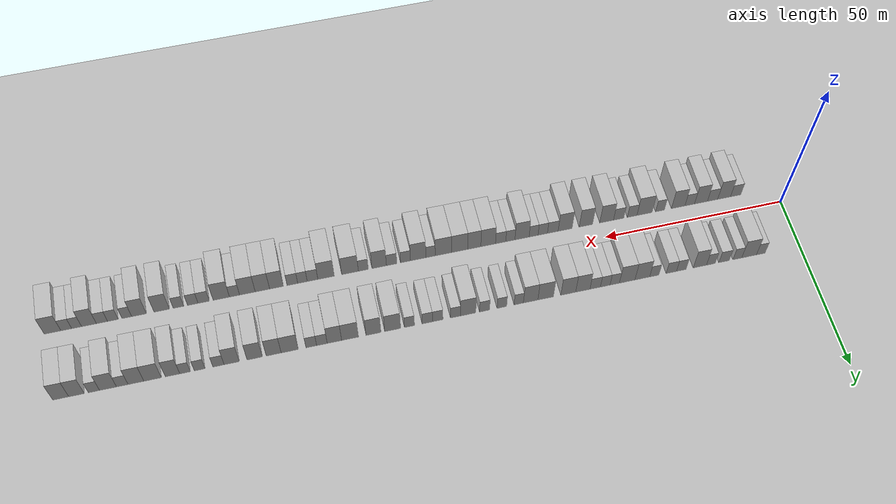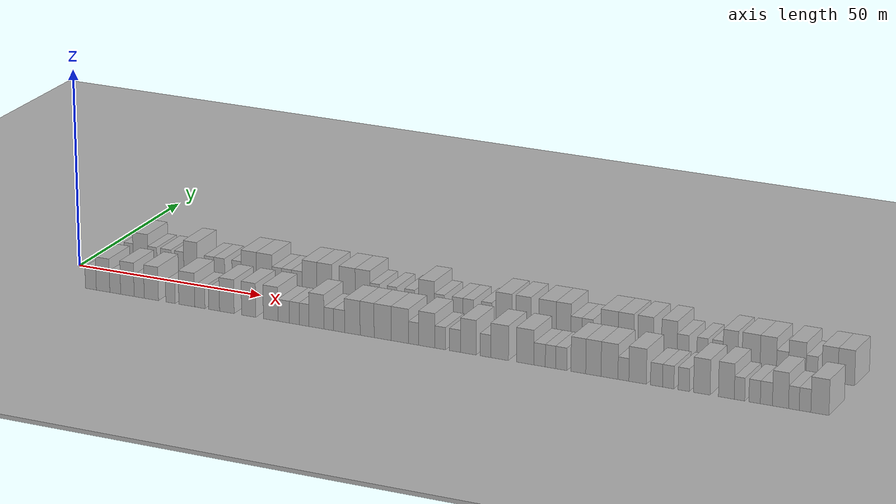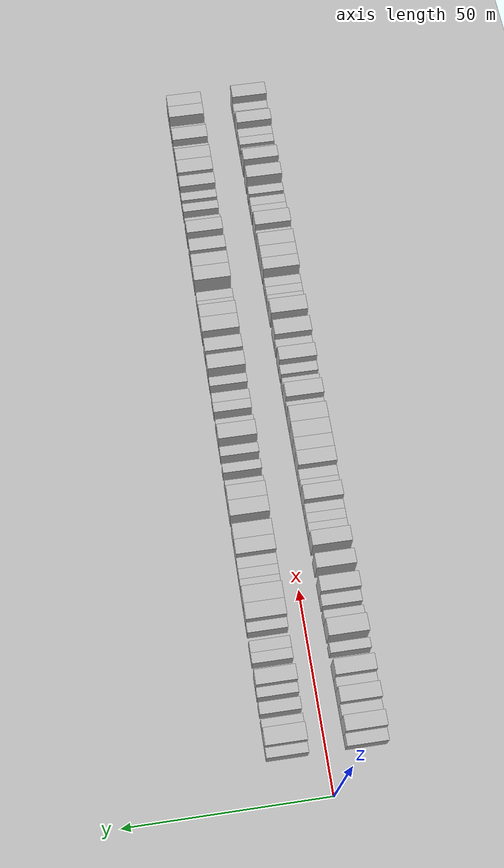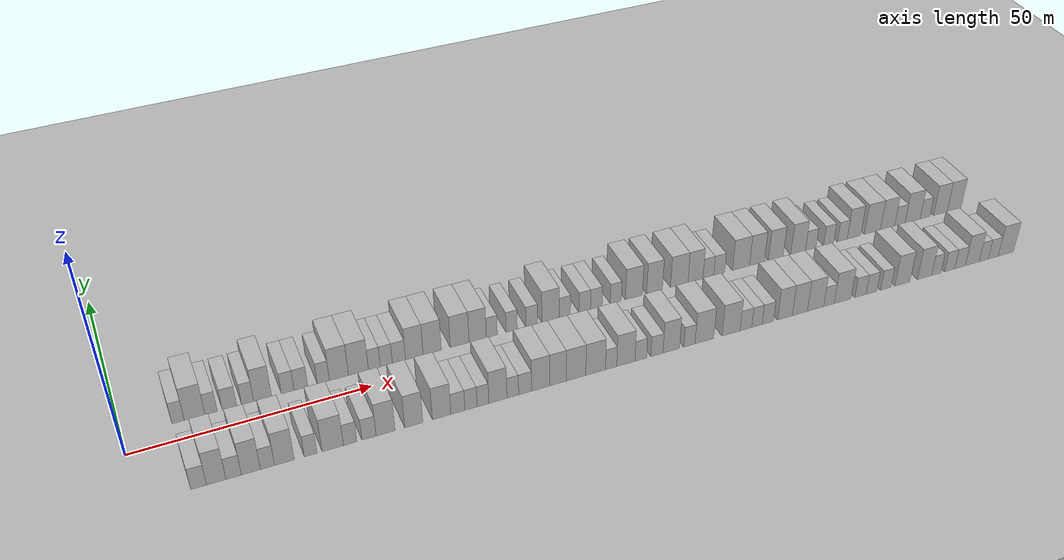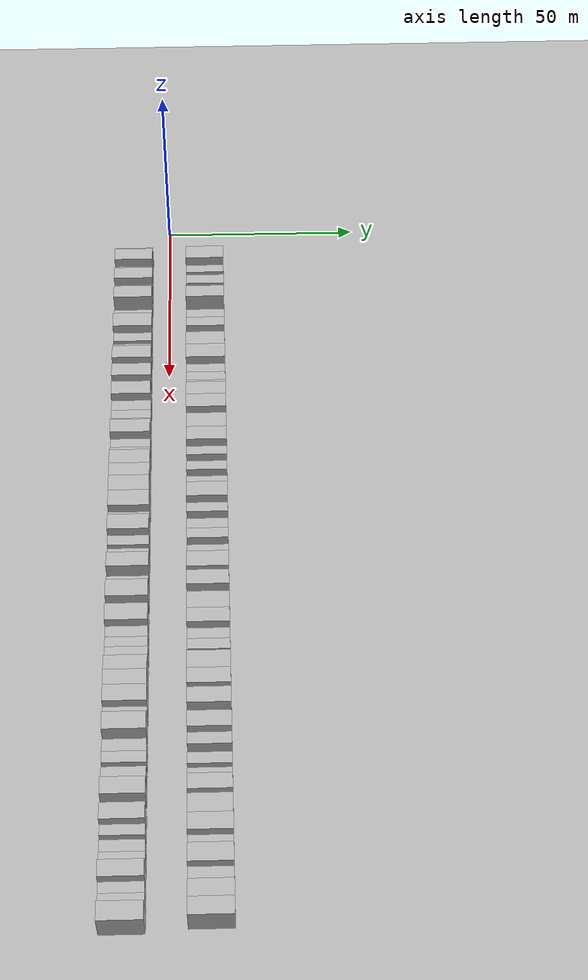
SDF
<?xml version="1.0" encoding="utf-8"?>

<sdf version="1.6">

   <world name="default">

      <gui fullscreen="0">

         <camera name="user_camera">

            <pose>-15 0 4.57585 0 0 0</pose>

            <view_controller>orbit</view_controller>

         </camera>

      </gui>

      <scene>

         <sky>

           <clouds>

             <speed>12</speed>

           </clouds>

         </sky>

         <ambient>0.4 0.4 0.4 1</ambient>

         <background>0.7 0.7 0.7 1</background>

         <shadows>1</shadows>

      </scene>

      <gravity>0 0 -9.8066</gravity>

      <magnetic_field>6e-06 2.3e-05 -4.2e-05</magnetic_field>

      <physics default="0" name="default_physics" type="ode">

         <ode>

            <solver>

               <type>quick</type>

               <iters>10</iters>

               <sor>1.0</sor>

               <use_dynamic_moi_rescaling>0</use_dynamic_moi_rescaling>

            </solver>

            <constraints>

               <cfm>0</cfm>

               <erp>0.2</erp>

               <contact_max_correcting_vel>100</contact_max_correcting_vel>

               <contact_surface_layer>0.001</contact_surface_layer>

            </constraints>

         </ode>

         <max_step_size>0.004</max_step_size>

         <real_time_factor>1</real_time_factor>

         <real_time_update_rate>250</real_time_update_rate>

      </physics>

      <light name="sun" type="directional">

         <cast_shadows>1</cast_shadows>

         <pose>0 0 10 0 0 0</pose>

         <diffuse>0.8 0.8 0.8 1</diffuse>

         <specular>0.2 0.2 0.2 1</specular>

         <attenuation>

            <range>1000</range>

            <constant>0.9</constant>

            <linear>0.01</linear>

            <quadratic>0.001</quadratic>

         </attenuation>

         <direction>-0.5 0.1 -0.9</direction>

      </light>

      <include>

         <name>ground_plane_1</name>

         <uri>model://HANNAS_ground_plane</uri>

         <pose>0 0 0  0 0 0</pose>

      </include>

      <include>

         <name>ground_plane_2</name>

         <uri>model://HANNAS_ground_plane</uri>

         <pose>100 0 0  0 0 0</pose>

      </include>

      <model name="building_1">

         <static>1</static>

         <pose frame="">11.2229 9.5000 0 0.000000 0.000000 1.570796</pose>

         <link name="link">

            <pose frame="">0 0 3.00 0 0 0</pose>

            <collision name="collision">

               <geometry>

                  <box>

                     <size>10.0000 2.4459 6.0000</size>

                  </box>

               </geometry>

               <max_contacts>10</max_contacts>

               <surface>

                  <contact>

                     <ode/>

                  </contact>

                  <bounce/>

                  <friction>

                     <torsional>

                        <ode/>

                     </torsional>

                     <ode/>

                  </friction>

               </surface>

            </collision>

            <visual name="visual">

               <cast_shadows>0</cast_shadows>

               <geometry>

                  <box>

                     <size>10.0000 2.4459 6.0000</size>

                  </box>

               </geometry>

               <material>

                  <script>

                     <uri>model://HANNAS_wall/materials/scripts</uri>

                     <uri>model://HANNAS_wall/materials/textures</uri>

                     <name>vrc/HANNAS_wall</name>

                  </script>

               </material>

            </visual>

            <self_collide>0</self_collide>

            <enable_wind>0</enable_wind>

            <kinematic>0</kinematic>

         </link>

      </model>

      <model name="building_2">

         <static>1</static>

         <pose frame="">14.5242 9.5000 0 0.000000 0.000000 1.570796</pose>

         <link name="link">

            <pose frame="">0 0 4.50 0 0 0</pose>

            <collision name="collision">

               <geometry>

                  <box>

                     <size>10.0000 4.1566 9.0000</size>

                  </box>

               </geometry>

               <max_contacts>10</max_contacts>

               <surface>

                  <contact>

                     <ode/>

                  </contact>

                  <bounce/>

                  <friction>

                     <torsional>

                        <ode/>

                     </torsional>

                     <ode/>

                  </friction>

               </surface>

            </collision>

            <visual name="visual">

               <cast_shadows>0</cast_shadows>

               <geometry>

                  <box>

                     <size>10.0000 4.1566 9.0000</size>

                  </box>

               </geometry>

               <material>

                  <script>

                     <uri>model://HANNAS_wall/materials/scripts</uri>

                     <uri>model://HANNAS_wall/materials/textures</uri>

                     <name>vrc/HANNAS_wall</name>

                  </script>

               </material>

            </visual>

            <self_collide>0</self_collide>

            <enable_wind>0</enable_wind>

            <kinematic>0</kinematic>

         </link>

      </model>

      <model name="building_3">

         <static>1</static>

         <pose frame="">17.8436 9.5000 0 0.000000 0.000000 1.570796</pose>

         <link name="link">

            <pose frame="">0 0 3.00 0 0 0</pose>

            <collision name="collision">

               <geometry>

                  <box>

                     <size>10.0000 2.4823 6.0000</size>

                  </box>

               </geometry>

               <max_contacts>10</max_contacts>

               <surface>

                  <contact>

                     <ode/>

                  </contact>

                  <bounce/>

                  <friction>

                     <torsional>

                        <ode/>

                     </torsional>

                     <ode/>

                  </friction>

               </surface>

            </collision>

            <visual name="visual">

               <cast_shadows>0</cast_shadows>

               <geometry>

                  <box>

                     <size>10.0000 2.4823 6.0000</size>

                  </box>

               </geometry>

               <material>

                  <script>

                     <uri>model://HANNAS_wall/materials/scripts</uri>

                     <uri>model://HANNAS_wall/materials/textures</uri>

                     <name>vrc/HANNAS_wall</name>

                  </script>

               </material>

            </visual>

            <self_collide>0</self_collide>

            <enable_wind>0</enable_wind>

            <kinematic>0</kinematic>

         </link>

      </model>

      <model name="building_4">

         <static>1</static>

         <pose frame="">21.5612 9.5000 0 0.000000 0.000000 1.570796</pose>

         <link name="link">

            <pose frame="">0 0 3.00 0 0 0</pose>

            <collision name="collision">

               <geometry>

                  <box>

                     <size>10.0000 2.9528 6.0000</size>

                  </box>

               </geometry>

               <max_contacts>10</max_contacts>

               <surface>

                  <contact>

                     <ode/>

                  </contact>

                  <bounce/>

                  <friction>

                     <torsional>

                        <ode/>

                     </torsional>

                     <ode/>

                  </friction>

               </surface>

            </collision>

            <visual name="visual">

               <cast_shadows>0</cast_shadows>

               <geometry>

                  <box>

                     <size>10.0000 2.9528 6.0000</size>

                  </box>

               </geometry>

               <material>

                  <script>

                     <uri>model://HANNAS_wall/materials/scripts</uri>

                     <uri>model://HANNAS_wall/materials/textures</uri>

                     <name>vrc/HANNAS_wall</name>

                  </script>

               </material>

            </visual>

            <self_collide>0</self_collide>

            <enable_wind>0</enable_wind>

            <kinematic>0</kinematic>

         </link>

      </model>

      <model name="building_5">

         <static>1</static>

         <pose frame="">25.2693 9.5000 0 0.000000 0.000000 1.570796</pose>

         <link name="link">

            <pose frame="">0 0 3.00 0 0 0</pose>

            <collision name="collision">

               <geometry>

                  <box>

                     <size>10.0000 2.4633 6.0000</size>

                  </box>

               </geometry>

               <max_contacts>10</max_contacts>

               <surface>

                  <contact>

                     <ode/>

                  </contact>

                  <bounce/>

                  <friction>

                     <torsional>

                        <ode/>

                     </torsional>

                     <ode/>

                  </friction>

               </surface>

            </collision>

            <visual name="visual">

               <cast_shadows>0</cast_shadows>

               <geometry>

                  <box>

                     <size>10.0000 2.4633 6.0000</size>

                  </box>

               </geometry>

               <material>

                  <script>

                     <uri>model://HANNAS_wall/materials/scripts</uri>

                     <uri>model://HANNAS_wall/materials/textures</uri>

                     <name>vrc/HANNAS_wall</name>

                  </script>

               </material>

            </visual>

            <self_collide>0</self_collide>

            <enable_wind>0</enable_wind>

            <kinematic>0</kinematic>

         </link>

      </model>

      <model name="building_6">

         <static>1</static>

         <pose frame="">28.3528 9.5000 0 0.000000 0.000000 1.570796</pose>

         <link name="link">

            <pose frame="">0 0 4.50 0 0 0</pose>

            <collision name="collision">

               <geometry>

                  <box>

                     <size>10.0000 3.7038 9.0000</size>

                  </box>

               </geometry>

               <max_contacts>10</max_contacts>

               <surface>

                  <contact>

                     <ode/>

                  </contact>

                  <bounce/>

                  <friction>

                     <torsional>

                        <ode/>

                     </torsional>

                     <ode/>

                  </friction>

               </surface>

            </collision>

            <visual name="visual">

               <cast_shadows>0</cast_shadows>

               <geometry>

                  <box>

                     <size>10.0000 3.7038 9.0000</size>

                  </box>

               </geometry>

               <material>

                  <script>

                     <uri>model://HANNAS_wall/materials/scripts</uri>

                     <uri>model://HANNAS_wall/materials/textures</uri>

                     <name>vrc/HANNAS_wall</name>

                  </script>

               </material>

            </visual>

            <self_collide>0</self_collide>

            <enable_wind>0</enable_wind>

            <kinematic>0</kinematic>

         </link>

      </model>

      <model name="building_7">

         <static>1</static>

         <pose frame="">33.5289 9.5000 0 0.000000 0.000000 1.570796</pose>

         <link name="link">

            <pose frame="">0 0 3.00 0 0 0</pose>

            <collision name="collision">

               <geometry>

                  <box>

                     <size>10.0000 2.6482 6.0000</size>

                  </box>

               </geometry>

               <max_contacts>10</max_contacts>

               <surface>

                  <contact>

                     <ode/>

                  </contact>

                  <bounce/>

                  <friction>

                     <torsional>

                        <ode/>

                     </torsional>

                     <ode/>

                  </friction>

               </surface>

            </collision>

            <visual name="visual">

               <cast_shadows>0</cast_shadows>

               <geometry>

                  <box>

                     <size>10.0000 2.6482 6.0000</size>

                  </box>

               </geometry>

               <material>

                  <script>

                     <uri>model://HANNAS_wall/materials/scripts</uri>

                     <uri>model://HANNAS_wall/materials/textures</uri>

                     <name>vrc/HANNAS_wall</name>

                  </script>

               </material>

            </visual>

            <self_collide>0</self_collide>

            <enable_wind>0</enable_wind>

            <kinematic>0</kinematic>

         </link>

      </model>

      <model name="building_8">

         <static>1</static>

         <pose frame="">36.3014 9.5000 0 0.000000 0.000000 1.570796</pose>

         <link name="link">

            <pose frame="">0 0 3.00 0 0 0</pose>

            <collision name="collision">

               <geometry>

                  <box>

                     <size>10.0000 2.8968 6.0000</size>

                  </box>

               </geometry>

               <max_contacts>10</max_contacts>

               <surface>

                  <contact>

                     <ode/>

                  </contact>

                  <bounce/>

                  <friction>

                     <torsional>

                        <ode/>

                     </torsional>

                     <ode/>

                  </friction>

               </surface>

            </collision>

            <visual name="visual">

               <cast_shadows>0</cast_shadows>

               <geometry>

                  <box>

                     <size>10.0000 2.8968 6.0000</size>

                  </box>

               </geometry>

               <material>

                  <script>

                     <uri>model://HANNAS_wall/materials/scripts</uri>

                     <uri>model://HANNAS_wall/materials/textures</uri>

                     <name>vrc/HANNAS_wall</name>

                  </script>

               </material>

            </visual>

            <self_collide>0</self_collide>

            <enable_wind>0</enable_wind>

            <kinematic>0</kinematic>

         </link>

      </model>

      <model name="building_9">

         <static>1</static>

         <pose frame="">41.0305 9.5000 0 0.000000 0.000000 1.570796</pose>

         <link name="link">

            <pose frame="">0 0 3.00 0 0 0</pose>

            <collision name="collision">

               <geometry>

                  <box>

                     <size>10.0000 2.5614 6.0000</size>

                  </box>

               </geometry>

               <max_contacts>10</max_contacts>

               <surface>

                  <contact>

                     <ode/>

                  </contact>

                  <bounce/>

                  <friction>

                     <torsional>

                        <ode/>

                     </torsional>

                     <ode/>

                  </friction>

               </surface>

            </collision>

            <visual name="visual">

               <cast_shadows>0</cast_shadows>

               <geometry>

                  <box>

                     <size>10.0000 2.5614 6.0000</size>

                  </box>

               </geometry>

               <material>

                  <script>

                     <uri>model://HANNAS_wall/materials/scripts</uri>

                     <uri>model://HANNAS_wall/materials/textures</uri>

                     <name>vrc/HANNAS_wall</name>

                  </script>

               </material>

            </visual>

            <self_collide>0</self_collide>

            <enable_wind>0</enable_wind>

            <kinematic>0</kinematic>

         </link>

      </model>

      <model name="building_10">

         <static>1</static>

         <pose frame="">44.3482 9.5000 0 0.000000 0.000000 1.570796</pose>

         <link name="link">

            <pose frame="">0 0 4.50 0 0 0</pose>

            <collision name="collision">

               <geometry>

                  <box>

                     <size>10.0000 4.0740 9.0000</size>

                  </box>

               </geometry>

               <max_contacts>10</max_contacts>

               <surface>

                  <contact>

                     <ode/>

                  </contact>

                  <bounce/>

                  <friction>

                     <torsional>

                        <ode/>

                     </torsional>

                     <ode/>

                  </friction>

               </surface>

            </collision>

            <visual name="visual">

               <cast_shadows>0</cast_shadows>

               <geometry>

                  <box>

                     <size>10.0000 4.0740 9.0000</size>

                  </box>

               </geometry>

               <material>

                  <script>

                     <uri>model://HANNAS_wall/materials/scripts</uri>

                     <uri>model://HANNAS_wall/materials/textures</uri>

                     <name>vrc/HANNAS_wall</name>

                  </script>

               </material>

            </visual>

            <self_collide>0</self_collide>

            <enable_wind>0</enable_wind>

            <kinematic>0</kinematic>

         </link>

      </model>

      <model name="building_11">

         <static>1</static>

         <pose frame="">48.5286 9.5000 0 0.000000 0.000000 1.570796</pose>

         <link name="link">

            <pose frame="">0 0 4.50 0 0 0</pose>

            <collision name="collision">

               <geometry>

                  <box>

                     <size>10.0000 4.2870 9.0000</size>

                  </box>

               </geometry>

               <max_contacts>10</max_contacts>

               <surface>

                  <contact>

                     <ode/>

                  </contact>

                  <bounce/>

                  <friction>

                     <torsional>

                        <ode/>

                     </torsional>

                     <ode/>

                  </friction>

               </surface>

            </collision>

            <visual name="visual">

               <cast_shadows>0</cast_shadows>

               <geometry>

                  <box>

                     <size>10.0000 4.2870 9.0000</size>

                  </box>

               </geometry>

               <material>

                  <script>

                     <uri>model://HANNAS_wall/materials/scripts</uri>

                     <uri>model://HANNAS_wall/materials/textures</uri>

                     <name>vrc/HANNAS_wall</name>

                  </script>

               </material>

            </visual>

            <self_collide>0</self_collide>

            <enable_wind>0</enable_wind>

            <kinematic>0</kinematic>

         </link>

      </model>

      <model name="building_12">

         <static>1</static>

         <pose frame="">51.9586 9.5000 0 0.000000 0.000000 1.570796</pose>

         <link name="link">

            <pose frame="">0 0 3.00 0 0 0</pose>

            <collision name="collision">

               <geometry>

                  <box>

                     <size>10.0000 2.5730 6.0000</size>

                  </box>

               </geometry>

               <max_contacts>10</max_contacts>

               <surface>

                  <contact>

                     <ode/>

                  </contact>

                  <bounce/>

                  <friction>

                     <torsional>

                        <ode/>

                     </torsional>

                     <ode/>

                  </friction>

               </surface>

            </collision>

            <visual name="visual">

               <cast_shadows>0</cast_shadows>

               <geometry>

                  <box>

                     <size>10.0000 2.5730 6.0000</size>

                  </box>

               </geometry>

               <material>

                  <script>

                     <uri>model://HANNAS_wall/materials/scripts</uri>

                     <uri>model://HANNAS_wall/materials/textures</uri>

                     <name>vrc/HANNAS_wall</name>

                  </script>

               </material>

            </visual>

            <self_collide>0</self_collide>

            <enable_wind>0</enable_wind>

            <kinematic>0</kinematic>

         </link>

      </model>

      <model name="building_13">

         <static>1</static>

         <pose frame="">54.5677 9.5000 0 0.000000 0.000000 1.570796</pose>

         <link name="link">

            <pose frame="">0 0 3.00 0 0 0</pose>

            <collision name="collision">

               <geometry>

                  <box>

                     <size>10.0000 2.6450 6.0000</size>

                  </box>

               </geometry>

               <max_contacts>10</max_contacts>

               <surface>

                  <contact>

                     <ode/>

                  </contact>

                  <bounce/>

                  <friction>

                     <torsional>

                        <ode/>

                     </torsional>

                     <ode/>

                  </friction>

               </surface>

            </collision>

            <visual name="visual">

               <cast_shadows>0</cast_shadows>

               <geometry>

                  <box>

                     <size>10.0000 2.6450 6.0000</size>

                  </box>

               </geometry>

               <material>

                  <script>

                     <uri>model://HANNAS_wall/materials/scripts</uri>

                     <uri>model://HANNAS_wall/materials/textures</uri>

                     <name>vrc/HANNAS_wall</name>

                  </script>

               </material>

            </visual>

            <self_collide>0</self_collide>

            <enable_wind>0</enable_wind>

            <kinematic>0</kinematic>

         </link>

      </model>

      <model name="building_14">

         <static>1</static>

         <pose frame="">57.3248 9.5000 0 0.000000 0.000000 1.570796</pose>

         <link name="link">

            <pose frame="">0 0 3.00 0 0 0</pose>

            <collision name="collision">

               <geometry>

                  <box>

                     <size>10.0000 2.8693 6.0000</size>

                  </box>

               </geometry>

               <max_contacts>10</max_contacts>

               <surface>

                  <contact>

                     <ode/>

                  </contact>

                  <bounce/>

                  <friction>

                     <torsional>

                        <ode/>

                     </torsional>

                     <ode/>

                  </friction>

               </surface>

            </collision>

            <visual name="visual">

               <cast_shadows>0</cast_shadows>

               <geometry>

                  <box>

                     <size>10.0000 2.8693 6.0000</size>

                  </box>

               </geometry>

               <material>

                  <script>

                     <uri>model://HANNAS_wall/materials/scripts</uri>

                     <uri>model://HANNAS_wall/materials/textures</uri>

                     <name>vrc/HANNAS_wall</name>

                  </script>

               </material>

            </visual>

            <self_collide>0</self_collide>

            <enable_wind>0</enable_wind>

            <kinematic>0</kinematic>

         </link>

      </model>

      <model name="building_15">

         <static>1</static>

         <pose frame="">60.7099 9.5000 0 0.000000 0.000000 1.570796</pose>

         <link name="link">

            <pose frame="">0 0 4.50 0 0 0</pose>

            <collision name="collision">

               <geometry>

                  <box>

                     <size>10.0000 3.9008 9.0000</size>

                  </box>

               </geometry>

               <max_contacts>10</max_contacts>

               <surface>

                  <contact>

                     <ode/>

                  </contact>

                  <bounce/>

                  <friction>

                     <torsional>

                        <ode/>

                     </torsional>

                     <ode/>

                  </friction>

               </surface>

            </collision>

            <visual name="visual">

               <cast_shadows>0</cast_shadows>

               <geometry>

                  <box>

                     <size>10.0000 3.9008 9.0000</size>

                  </box>

               </geometry>

               <material>

                  <script>

                     <uri>model://HANNAS_wall/materials/scripts</uri>

                     <uri>model://HANNAS_wall/materials/textures</uri>

                     <name>vrc/HANNAS_wall</name>

                  </script>

               </material>

            </visual>

            <self_collide>0</self_collide>

            <enable_wind>0</enable_wind>

            <kinematic>0</kinematic>

         </link>

      </model>

      <model name="building_16">

         <static>1</static>

         <pose frame="">64.6893 9.5000 0 0.000000 0.000000 1.570796</pose>

         <link name="link">

            <pose frame="">0 0 4.50 0 0 0</pose>

            <collision name="collision">

               <geometry>

                  <box>

                     <size>10.0000 4.0580 9.0000</size>

                  </box>

               </geometry>

               <max_contacts>10</max_contacts>

               <surface>

                  <contact>

                     <ode/>

                  </contact>

                  <bounce/>

                  <friction>

                     <torsional>

                        <ode/>

                     </torsional>

                     <ode/>

                  </friction>

               </surface>

            </collision>

            <visual name="visual">

               <cast_shadows>0</cast_shadows>

               <geometry>

                  <box>

                     <size>10.0000 4.0580 9.0000</size>

                  </box>

               </geometry>

               <material>

                  <script>

                     <uri>model://HANNAS_wall/materials/scripts</uri>

                     <uri>model://HANNAS_wall/materials/textures</uri>

                     <name>vrc/HANNAS_wall</name>

                  </script>

               </material>

            </visual>

            <self_collide>0</self_collide>

            <enable_wind>0</enable_wind>

            <kinematic>0</kinematic>

         </link>

      </model>

      <model name="building_17">

         <static>1</static>

         <pose frame="">70.8295 9.5000 0 0.000000 0.000000 1.570796</pose>

         <link name="link">

            <pose frame="">0 0 4.50 0 0 0</pose>

            <collision name="collision">

               <geometry>

                  <box>

                     <size>10.0000 4.2225 9.0000</size>

                  </box>

               </geometry>

               <max_contacts>10</max_contacts>

               <surface>

                  <contact>

                     <ode/>

                  </contact>

                  <bounce/>

                  <friction>

                     <torsional>

                        <ode/>

                     </torsional>

                     <ode/>

                  </friction>

               </surface>

            </collision>

            <visual name="visual">

               <cast_shadows>0</cast_shadows>

               <geometry>

                  <box>

                     <size>10.0000 4.2225 9.0000</size>

                  </box>

               </geometry>

               <material>

                  <script>

                     <uri>model://HANNAS_wall/materials/scripts</uri>

                     <uri>model://HANNAS_wall/materials/textures</uri>

                     <name>vrc/HANNAS_wall</name>

                  </script>

               </material>

            </visual>

            <self_collide>0</self_collide>

            <enable_wind>0</enable_wind>

            <kinematic>0</kinematic>

         </link>

      </model>

      <model name="building_18">

         <static>1</static>

         <pose frame="">74.9079 9.5000 0 0.000000 0.000000 1.570796</pose>

         <link name="link">

            <pose frame="">0 0 4.50 0 0 0</pose>

            <collision name="collision">

               <geometry>

                  <box>

                     <size>10.0000 3.9343 9.0000</size>

                  </box>

               </geometry>

               <max_contacts>10</max_contacts>

               <surface>

                  <contact>

                     <ode/>

                  </contact>

                  <bounce/>

                  <friction>

                     <torsional>

                        <ode/>

                     </torsional>

                     <ode/>

                  </friction>

               </surface>

            </collision>

            <visual name="visual">

               <cast_shadows>0</cast_shadows>

               <geometry>

                  <box>

                     <size>10.0000 3.9343 9.0000</size>

                  </box>

               </geometry>

               <material>

                  <script>

                     <uri>model://HANNAS_wall/materials/scripts</uri>

                     <uri>model://HANNAS_wall/materials/textures</uri>

                     <name>vrc/HANNAS_wall</name>

                  </script>

               </material>

            </visual>

            <self_collide>0</self_collide>

            <enable_wind>0</enable_wind>

            <kinematic>0</kinematic>

         </link>

      </model>

      <model name="building_19">

         <static>1</static>

         <pose frame="">78.1344 9.5000 0 0.000000 0.000000 1.570796</pose>

         <link name="link">

            <pose frame="">0 0 3.00 0 0 0</pose>

            <collision name="collision">

               <geometry>

                  <box>

                     <size>10.0000 2.5186 6.0000</size>

                  </box>

               </geometry>

               <max_contacts>10</max_contacts>

               <surface>

                  <contact>

                     <ode/>

                  </contact>

                  <bounce/>

                  <friction>

                     <torsional>

                        <ode/>

                     </torsional>

                     <ode/>

                  </friction>

               </surface>

            </collision>

            <visual name="visual">

               <cast_shadows>0</cast_shadows>

               <geometry>

                  <box>

                     <size>10.0000 2.5186 6.0000</size>

                  </box>

               </geometry>

               <material>

                  <script>

                     <uri>model://HANNAS_wall/materials/scripts</uri>

                     <uri>model://HANNAS_wall/materials/textures</uri>

                     <name>vrc/HANNAS_wall</name>

                  </script>

               </material>

            </visual>

            <self_collide>0</self_collide>

            <enable_wind>0</enable_wind>

            <kinematic>0</kinematic>

         </link>

      </model>

      <model name="building_20">

         <static>1</static>

         <pose frame="">82.6851 9.5000 0 0.000000 0.000000 1.570796</pose>

         <link name="link">

            <pose frame="">0 0 3.00 0 0 0</pose>

            <collision name="collision">

               <geometry>

                  <box>

                     <size>10.0000 2.5830 6.0000</size>

                  </box>

               </geometry>

               <max_contacts>10</max_contacts>

               <surface>

                  <contact>

                     <ode/>

                  </contact>

                  <bounce/>

                  <friction>

                     <torsional>

                        <ode/>

                     </torsional>

                     <ode/>

                  </friction>

               </surface>

            </collision>

            <visual name="visual">

               <cast_shadows>0</cast_shadows>

               <geometry>

                  <box>

                     <size>10.0000 2.5830 6.0000</size>

                  </box>

               </geometry>

               <material>

                  <script>

                     <uri>model://HANNAS_wall/materials/scripts</uri>

                     <uri>model://HANNAS_wall/materials/textures</uri>

                     <name>vrc/HANNAS_wall</name>

                  </script>

               </material>

            </visual>

            <self_collide>0</self_collide>

            <enable_wind>0</enable_wind>

            <kinematic>0</kinematic>

         </link>

      </model>

      <model name="building_21">

         <static>1</static>

         <pose frame="">87.3327 9.5000 0 0.000000 0.000000 1.570796</pose>

         <link name="link">

            <pose frame="">0 0 3.00 0 0 0</pose>

            <collision name="collision">

               <geometry>

                  <box>

                     <size>10.0000 2.7122 6.0000</size>

                  </box>

               </geometry>

               <max_contacts>10</max_contacts>

               <surface>

                  <contact>

                     <ode/>

                  </contact>

                  <bounce/>

                  <friction>

                     <torsional>

                        <ode/>

                     </torsional>

                     <ode/>

                  </friction>

               </surface>

            </collision>

            <visual name="visual">

               <cast_shadows>0</cast_shadows>

               <geometry>

                  <box>

                     <size>10.0000 2.7122 6.0000</size>

                  </box>

               </geometry>

               <material>

                  <script>

                     <uri>model://HANNAS_wall/materials/scripts</uri>

                     <uri>model://HANNAS_wall/materials/textures</uri>

                     <name>vrc/HANNAS_wall</name>

                  </script>

               </material>

            </visual>

            <self_collide>0</self_collide>

            <enable_wind>0</enable_wind>

            <kinematic>0</kinematic>

         </link>

      </model>

      <model name="building_22">

         <static>1</static>

         <pose frame="">91.7432 9.5000 0 0.000000 0.000000 1.570796</pose>

         <link name="link">

            <pose frame="">0 0 4.50 0 0 0</pose>

            <collision name="collision">

               <geometry>

                  <box>

                     <size>10.0000 4.1087 9.0000</size>

                  </box>

               </geometry>

               <max_contacts>10</max_contacts>

               <surface>

                  <contact>

                     <ode/>

                  </contact>

                  <bounce/>

                  <friction>

                     <torsional>

                        <ode/>

                     </torsional>

                     <ode/>

                  </friction>

               </surface>

            </collision>

            <visual name="visual">

               <cast_shadows>0</cast_shadows>

               <geometry>

                  <box>

                     <size>10.0000 4.1087 9.0000</size>

                  </box>

               </geometry>

               <material>

                  <script>

                     <uri>model://HANNAS_wall/materials/scripts</uri>

                     <uri>model://HANNAS_wall/materials/textures</uri>

                     <name>vrc/HANNAS_wall</name>

                  </script>

               </material>

            </visual>

            <self_collide>0</self_collide>

            <enable_wind>0</enable_wind>

            <kinematic>0</kinematic>

         </link>

      </model>

      <model name="building_23">

         <static>1</static>

         <pose frame="">95.1326 9.5000 0 0.000000 0.000000 1.570796</pose>

         <link name="link">

            <pose frame="">0 0 3.00 0 0 0</pose>

            <collision name="collision">

               <geometry>

                  <box>

                     <size>10.0000 2.6700 6.0000</size>

                  </box>

               </geometry>

               <max_contacts>10</max_contacts>

               <surface>

                  <contact>

                     <ode/>

                  </contact>

                  <bounce/>

                  <friction>

                     <torsional>

                        <ode/>

                     </torsional>

                     <ode/>

                  </friction>

               </surface>

            </collision>

            <visual name="visual">

               <cast_shadows>0</cast_shadows>

               <geometry>

                  <box>

                     <size>10.0000 2.6700 6.0000</size>

                  </box>

               </geometry>

               <material>

                  <script>

                     <uri>model://HANNAS_wall/materials/scripts</uri>

                     <uri>model://HANNAS_wall/materials/textures</uri>

                     <name>vrc/HANNAS_wall</name>

                  </script>

               </material>

            </visual>

            <self_collide>0</self_collide>

            <enable_wind>0</enable_wind>

            <kinematic>0</kinematic>

         </link>

      </model>

      <model name="building_24">

         <static>1</static>

         <pose frame="">99.8553 9.5000 0 0.000000 0.000000 1.570796</pose>

         <link name="link">

            <pose frame="">0 0 3.00 0 0 0</pose>

            <collision name="collision">

               <geometry>

                  <box>

                     <size>10.0000 2.7754 6.0000</size>

                  </box>

               </geometry>

               <max_contacts>10</max_contacts>

               <surface>

                  <contact>

                     <ode/>

                  </contact>

                  <bounce/>

                  <friction>

                     <torsional>

                        <ode/>

                     </torsional>

                     <ode/>

                  </friction>

               </surface>

            </collision>

            <visual name="visual">

               <cast_shadows>0</cast_shadows>

               <geometry>

                  <box>

                     <size>10.0000 2.7754 6.0000</size>

                  </box>

               </geometry>

               <material>

                  <script>

                     <uri>model://HANNAS_wall/materials/scripts</uri>

                     <uri>model://HANNAS_wall/materials/textures</uri>

                     <name>vrc/HANNAS_wall</name>

                  </script>

               </material>

            </visual>

            <self_collide>0</self_collide>

            <enable_wind>0</enable_wind>

            <kinematic>0</kinematic>

         </link>

      </model>

      <model name="building_25">

         <static>1</static>

         <pose frame="">102.6334 9.5000 0 0.000000 0.000000 1.570796</pose>

         <link name="link">

            <pose frame="">0 0 3.00 0 0 0</pose>

            <collision name="collision">

               <geometry>

                  <box>

                     <size>10.0000 2.7807 6.0000</size>

                  </box>

               </geometry>

               <max_contacts>10</max_contacts>

               <surface>

                  <contact>

                     <ode/>

                  </contact>

                  <bounce/>

                  <friction>

                     <torsional>

                        <ode/>

                     </torsional>

                     <ode/>

                  </friction>

               </surface>

            </collision>

            <visual name="visual">

               <cast_shadows>0</cast_shadows>

               <geometry>

                  <box>

                     <size>10.0000 2.7807 6.0000</size>

                  </box>

               </geometry>

               <material>

                  <script>

                     <uri>model://HANNAS_wall/materials/scripts</uri>

                     <uri>model://HANNAS_wall/materials/textures</uri>

                     <name>vrc/HANNAS_wall</name>

                  </script>

               </material>

            </visual>

            <self_collide>0</self_collide>

            <enable_wind>0</enable_wind>

            <kinematic>0</kinematic>

         </link>

      </model>

      <model name="building_26">

         <static>1</static>

         <pose frame="">107.3550 9.5000 0 0.000000 0.000000 1.570796</pose>

         <link name="link">

            <pose frame="">0 0 3.00 0 0 0</pose>

            <collision name="collision">

               <geometry>

                  <box>

                     <size>10.0000 2.6625 6.0000</size>

                  </box>

               </geometry>

               <max_contacts>10</max_contacts>

               <surface>

                  <contact>

                     <ode/>

                  </contact>

                  <bounce/>

                  <friction>

                     <torsional>

                        <ode/>

                     </torsional>

                     <ode/>

                  </friction>

               </surface>

            </collision>

            <visual name="visual">

               <cast_shadows>0</cast_shadows>

               <geometry>

                  <box>

                     <size>10.0000 2.6625 6.0000</size>

                  </box>

               </geometry>

               <material>

                  <script>

                     <uri>model://HANNAS_wall/materials/scripts</uri>

                     <uri>model://HANNAS_wall/materials/textures</uri>

                     <name>vrc/HANNAS_wall</name>

                  </script>

               </material>

            </visual>

            <self_collide>0</self_collide>

            <enable_wind>0</enable_wind>

            <kinematic>0</kinematic>

         </link>

      </model>

      <model name="building_27">

         <static>1</static>

         <pose frame="">111.7815 9.5000 0 0.000000 0.000000 1.570796</pose>

         <link name="link">

            <pose frame="">0 0 4.50 0 0 0</pose>

            <collision name="collision">

               <geometry>

                  <box>

                     <size>10.0000 4.1905 9.0000</size>

                  </box>

               </geometry>

               <max_contacts>10</max_contacts>

               <surface>

                  <contact>

                     <ode/>

                  </contact>

                  <bounce/>

                  <friction>

                     <torsional>

                        <ode/>

                     </torsional>

                     <ode/>

                  </friction>

               </surface>

            </collision>

            <visual name="visual">

               <cast_shadows>0</cast_shadows>

               <geometry>

                  <box>

                     <size>10.0000 4.1905 9.0000</size>

                  </box>

               </geometry>

               <material>

                  <script>

                     <uri>model://HANNAS_wall/materials/scripts</uri>

                     <uri>model://HANNAS_wall/materials/textures</uri>

                     <name>vrc/HANNAS_wall</name>

                  </script>

               </material>

            </visual>

            <self_collide>0</self_collide>

            <enable_wind>0</enable_wind>

            <kinematic>0</kinematic>

         </link>

      </model>

      <model name="building_28">

         <static>1</static>

         <pose frame="">116.8333 9.5000 0 0.000000 0.000000 1.570796</pose>

         <link name="link">

            <pose frame="">0 0 4.50 0 0 0</pose>

            <collision name="collision">

               <geometry>

                  <box>

                     <size>10.0000 3.9132 9.0000</size>

                  </box>

               </geometry>

               <max_contacts>10</max_contacts>

               <surface>

                  <contact>

                     <ode/>

                  </contact>

                  <bounce/>

                  <friction>

                     <torsional>

                        <ode/>

                     </torsional>

                     <ode/>

                  </friction>

               </surface>

            </collision>

            <visual name="visual">

               <cast_shadows>0</cast_shadows>

               <geometry>

                  <box>

                     <size>10.0000 3.9132 9.0000</size>

                  </box>

               </geometry>

               <material>

                  <script>

                     <uri>model://HANNAS_wall/materials/scripts</uri>

                     <uri>model://HANNAS_wall/materials/textures</uri>

                     <name>vrc/HANNAS_wall</name>

                  </script>

               </material>

            </visual>

            <self_collide>0</self_collide>

            <enable_wind>0</enable_wind>

            <kinematic>0</kinematic>

         </link>

      </model>

      <model name="building_29">

         <static>1</static>

         <pose frame="">122.9893 9.5000 0 0.000000 0.000000 1.570796</pose>

         <link name="link">

            <pose frame="">0 0 4.50 0 0 0</pose>

            <collision name="collision">

               <geometry>

                  <box>

                     <size>10.0000 4.3988 9.0000</size>

                  </box>

               </geometry>

               <max_contacts>10</max_contacts>

               <surface>

                  <contact>

                     <ode/>

                  </contact>

                  <bounce/>

                  <friction>

                     <torsional>

                        <ode/>

                     </torsional>

                     <ode/>

                  </friction>

               </surface>

            </collision>

            <visual name="visual">

               <cast_shadows>0</cast_shadows>

               <geometry>

                  <box>

                     <size>10.0000 4.3988 9.0000</size>

                  </box>

               </geometry>

               <material>

                  <script>

                     <uri>model://HANNAS_wall/materials/scripts</uri>

                     <uri>model://HANNAS_wall/materials/textures</uri>

                     <name>vrc/HANNAS_wall</name>

                  </script>

               </material>

            </visual>

            <self_collide>0</self_collide>

            <enable_wind>0</enable_wind>

            <kinematic>0</kinematic>

         </link>

      </model>

      <model name="building_30">

         <static>1</static>

         <pose frame="">127.0721 9.5000 0 0.000000 0.000000 1.570796</pose>

         <link name="link">

            <pose frame="">0 0 4.50 0 0 0</pose>

            <collision name="collision">

               <geometry>

                  <box>

                     <size>10.0000 3.7666 9.0000</size>

                  </box>

               </geometry>

               <max_contacts>10</max_contacts>

               <surface>

                  <contact>

                     <ode/>

                  </contact>

                  <bounce/>

                  <friction>

                     <torsional>

                        <ode/>

                     </torsional>

                     <ode/>

                  </friction>

               </surface>

            </collision>

            <visual name="visual">

               <cast_shadows>0</cast_shadows>

               <geometry>

                  <box>

                     <size>10.0000 3.7666 9.0000</size>

                  </box>

               </geometry>

               <material>

                  <script>

                     <uri>model://HANNAS_wall/materials/scripts</uri>

                     <uri>model://HANNAS_wall/materials/textures</uri>

                     <name>vrc/HANNAS_wall</name>

                  </script>

               </material>

            </visual>

            <self_collide>0</self_collide>

            <enable_wind>0</enable_wind>

            <kinematic>0</kinematic>

         </link>

      </model>

      <model name="building_31">

         <static>1</static>

         <pose frame="">130.3317 9.5000 0 0.000000 0.000000 1.570796</pose>

         <link name="link">

            <pose frame="">0 0 3.00 0 0 0</pose>

            <collision name="collision">

               <geometry>

                  <box>

                     <size>10.0000 2.7527 6.0000</size>

                  </box>

               </geometry>

               <max_contacts>10</max_contacts>

               <surface>

                  <contact>

                     <ode/>

                  </contact>

                  <bounce/>

                  <friction>

                     <torsional>

                        <ode/>

                     </torsional>

                     <ode/>

                  </friction>

               </surface>

            </collision>

            <visual name="visual">

               <cast_shadows>0</cast_shadows>

               <geometry>

                  <box>

                     <size>10.0000 2.7527 6.0000</size>

                  </box>

               </geometry>

               <material>

                  <script>

                     <uri>model://HANNAS_wall/materials/scripts</uri>

                     <uri>model://HANNAS_wall/materials/textures</uri>

                     <name>vrc/HANNAS_wall</name>

                  </script>

               </material>

            </visual>

            <self_collide>0</self_collide>

            <enable_wind>0</enable_wind>

            <kinematic>0</kinematic>

         </link>

      </model>

      <model name="building_32">

         <static>1</static>

         <pose frame="">133.1014 9.5000 0 0.000000 0.000000 1.570796</pose>

         <link name="link">

            <pose frame="">0 0 3.00 0 0 0</pose>

            <collision name="collision">

               <geometry>

                  <box>

                     <size>10.0000 2.7868 6.0000</size>

                  </box>

               </geometry>

               <max_contacts>10</max_contacts>

               <surface>

                  <contact>

                     <ode/>

                  </contact>

                  <bounce/>

                  <friction>

                     <torsional>

                        <ode/>

                     </torsional>

                     <ode/>

                  </friction>

               </surface>

            </collision>

            <visual name="visual">

               <cast_shadows>0</cast_shadows>

               <geometry>

                  <box>

                     <size>10.0000 2.7868 6.0000</size>

                  </box>

               </geometry>

               <material>

                  <script>

                     <uri>model://HANNAS_wall/materials/scripts</uri>

                     <uri>model://HANNAS_wall/materials/textures</uri>

                     <name>vrc/HANNAS_wall</name>

                  </script>

               </material>

            </visual>

            <self_collide>0</self_collide>

            <enable_wind>0</enable_wind>

            <kinematic>0</kinematic>

         </link>

      </model>

      <model name="building_33">

         <static>1</static>

         <pose frame="">138.6992 9.5000 0 0.000000 0.000000 1.570796</pose>

         <link name="link">

            <pose frame="">0 0 4.50 0 0 0</pose>

            <collision name="collision">

               <geometry>

                  <box>

                     <size>10.0000 4.4088 9.0000</size>

                  </box>

               </geometry>

               <max_contacts>10</max_contacts>

               <surface>

                  <contact>

                     <ode/>

                  </contact>

                  <bounce/>

                  <friction>

                     <torsional>

                        <ode/>

                     </torsional>

                     <ode/>

                  </friction>

               </surface>

            </collision>

            <visual name="visual">

               <cast_shadows>0</cast_shadows>

               <geometry>

                  <box>

                     <size>10.0000 4.4088 9.0000</size>

                  </box>

               </geometry>

               <material>

                  <script>

                     <uri>model://HANNAS_wall/materials/scripts</uri>

                     <uri>model://HANNAS_wall/materials/textures</uri>

                     <name>vrc/HANNAS_wall</name>

                  </script>

               </material>

            </visual>

            <self_collide>0</self_collide>

            <enable_wind>0</enable_wind>

            <kinematic>0</kinematic>

         </link>

      </model>

      <model name="building_34">

         <static>1</static>

         <pose frame="">142.8364 9.5000 0 0.000000 0.000000 1.570796</pose>

         <link name="link">

            <pose frame="">0 0 4.50 0 0 0</pose>

            <collision name="collision">

               <geometry>

                  <box>

                     <size>10.0000 3.8655 9.0000</size>

                  </box>

               </geometry>

               <max_contacts>10</max_contacts>

               <surface>

                  <contact>

                     <ode/>

                  </contact>

                  <bounce/>

                  <friction>

                     <torsional>

                        <ode/>

                     </torsional>

                     <ode/>

                  </friction>

               </surface>

            </collision>

            <visual name="visual">

               <cast_shadows>0</cast_shadows>

               <geometry>

                  <box>

                     <size>10.0000 3.8655 9.0000</size>

                  </box>

               </geometry>

               <material>

                  <script>

                     <uri>model://HANNAS_wall/materials/scripts</uri>

                     <uri>model://HANNAS_wall/materials/textures</uri>

                     <name>vrc/HANNAS_wall</name>

                  </script>

               </material>

            </visual>

            <self_collide>0</self_collide>

            <enable_wind>0</enable_wind>

            <kinematic>0</kinematic>

         </link>

      </model>

      <model name="building_35">

         <static>1</static>

         <pose frame="">147.7309 9.5000 0 0.000000 0.000000 1.570796</pose>

         <link name="link">

            <pose frame="">0 0 4.50 0 0 0</pose>

            <collision name="collision">

               <geometry>

                  <box>

                     <size>10.0000 3.9235 9.0000</size>

                  </box>

               </geometry>

               <max_contacts>10</max_contacts>

               <surface>

                  <contact>

                     <ode/>

                  </contact>

                  <bounce/>

                  <friction>

                     <torsional>

                        <ode/>

                     </torsional>

                     <ode/>

                  </friction>

               </surface>

            </collision>

            <visual name="visual">

               <cast_shadows>0</cast_shadows>

               <geometry>

                  <box>

                     <size>10.0000 3.9235 9.0000</size>

                  </box>

               </geometry>

               <material>

                  <script>

                     <uri>model://HANNAS_wall/materials/scripts</uri>

                     <uri>model://HANNAS_wall/materials/textures</uri>

                     <name>vrc/HANNAS_wall</name>

                  </script>

               </material>

            </visual>

            <self_collide>0</self_collide>

            <enable_wind>0</enable_wind>

            <kinematic>0</kinematic>

         </link>

      </model>

      <model name="building_36">

         <static>1</static>

         <pose frame="">153.6406 9.5000 0 0.000000 0.000000 1.570796</pose>

         <link name="link">

            <pose frame="">0 0 4.50 0 0 0</pose>

            <collision name="collision">

               <geometry>

                  <box>

                     <size>10.0000 3.8959 9.0000</size>

                  </box>

               </geometry>

               <max_contacts>10</max_contacts>

               <surface>

                  <contact>

                     <ode/>

                  </contact>

                  <bounce/>

                  <friction>

                     <torsional>

                        <ode/>

                     </torsional>

                     <ode/>

                  </friction>

               </surface>

            </collision>

            <visual name="visual">

               <cast_shadows>0</cast_shadows>

               <geometry>

                  <box>

                     <size>10.0000 3.8959 9.0000</size>

                  </box>

               </geometry>

               <material>

                  <script>

                     <uri>model://HANNAS_wall/materials/scripts</uri>

                     <uri>model://HANNAS_wall/materials/textures</uri>

                     <name>vrc/HANNAS_wall</name>

                  </script>

               </material>

            </visual>

            <self_collide>0</self_collide>

            <enable_wind>0</enable_wind>

            <kinematic>0</kinematic>

         </link>

      </model>

      <model name="building_37">

         <static>1</static>

         <pose frame="">157.0237 9.5000 0 0.000000 0.000000 1.570796</pose>

         <link name="link">

            <pose frame="">0 0 3.00 0 0 0</pose>

            <collision name="collision">

               <geometry>

                  <box>

                     <size>10.0000 2.8703 6.0000</size>

                  </box>

               </geometry>

               <max_contacts>10</max_contacts>

               <surface>

                  <contact>

                     <ode/>

                  </contact>

                  <bounce/>

                  <friction>

                     <torsional>

                        <ode/>

                     </torsional>

                     <ode/>

                  </friction>

               </surface>

            </collision>

            <visual name="visual">

               <cast_shadows>0</cast_shadows>

               <geometry>

                  <box>

                     <size>10.0000 2.8703 6.0000</size>

                  </box>

               </geometry>

               <material>

                  <script>

                     <uri>model://HANNAS_wall/materials/scripts</uri>

                     <uri>model://HANNAS_wall/materials/textures</uri>

                     <name>vrc/HANNAS_wall</name>

                  </script>

               </material>

            </visual>

            <self_collide>0</self_collide>

            <enable_wind>0</enable_wind>

            <kinematic>0</kinematic>

         </link>

      </model>

      <model name="building_38">

         <static>1</static>

         <pose frame="">161.8284 9.5000 0 0.000000 0.000000 1.570796</pose>

         <link name="link">

            <pose frame="">0 0 3.00 0 0 0</pose>

            <collision name="collision">

               <geometry>

                  <box>

                     <size>10.0000 2.7392 6.0000</size>

                  </box>

               </geometry>

               <max_contacts>10</max_contacts>

               <surface>

                  <contact>

                     <ode/>

                  </contact>

                  <bounce/>

                  <friction>

                     <torsional>

                        <ode/>

                     </torsional>

                     <ode/>

                  </friction>

               </surface>

            </collision>

            <visual name="visual">

               <cast_shadows>0</cast_shadows>

               <geometry>

                  <box>

                     <size>10.0000 2.7392 6.0000</size>

                  </box>

               </geometry>

               <material>

                  <script>

                     <uri>model://HANNAS_wall/materials/scripts</uri>

                     <uri>model://HANNAS_wall/materials/textures</uri>

                     <name>vrc/HANNAS_wall</name>

                  </script>

               </material>

            </visual>

            <self_collide>0</self_collide>

            <enable_wind>0</enable_wind>

            <kinematic>0</kinematic>

         </link>

      </model>

      <model name="building_39">

         <static>1</static>

         <pose frame="">165.5387 9.5000 0 0.000000 0.000000 1.570796</pose>

         <link name="link">

            <pose frame="">0 0 3.00 0 0 0</pose>

            <collision name="collision">

               <geometry>

                  <box>

                     <size>10.0000 2.6815 6.0000</size>

                  </box>

               </geometry>

               <max_contacts>10</max_contacts>

               <surface>

                  <contact>

                     <ode/>

                  </contact>

                  <bounce/>

                  <friction>

                     <torsional>

                        <ode/>

                     </torsional>

                     <ode/>

                  </friction>

               </surface>

            </collision>

            <visual name="visual">

               <cast_shadows>0</cast_shadows>

               <geometry>

                  <box>

                     <size>10.0000 2.6815 6.0000</size>

                  </box>

               </geometry>

               <material>

                  <script>

                     <uri>model://HANNAS_wall/materials/scripts</uri>

                     <uri>model://HANNAS_wall/materials/textures</uri>

                     <name>vrc/HANNAS_wall</name>

                  </script>

               </material>

            </visual>

            <self_collide>0</self_collide>

            <enable_wind>0</enable_wind>

            <kinematic>0</kinematic>

         </link>

      </model>

      <model name="building_40">

         <static>1</static>

         <pose frame="">168.7153 9.5000 0 0.000000 0.000000 1.570796</pose>

         <link name="link">

            <pose frame="">0 0 4.50 0 0 0</pose>

            <collision name="collision">

               <geometry>

                  <box>

                     <size>10.0000 3.6718 9.0000</size>

                  </box>

               </geometry>

               <max_contacts>10</max_contacts>

               <surface>

                  <contact>

                     <ode/>

                  </contact>

                  <bounce/>

                  <friction>

                     <torsional>

                        <ode/>

                     </torsional>

                     <ode/>

                  </friction>

               </surface>

            </collision>

            <visual name="visual">

               <cast_shadows>0</cast_shadows>

               <geometry>

                  <box>

                     <size>10.0000 3.6718 9.0000</size>

                  </box>

               </geometry>

               <material>

                  <script>

                     <uri>model://HANNAS_wall/materials/scripts</uri>

                     <uri>model://HANNAS_wall/materials/textures</uri>

                     <name>vrc/HANNAS_wall</name>

                  </script>

               </material>

            </visual>

            <self_collide>0</self_collide>

            <enable_wind>0</enable_wind>

            <kinematic>0</kinematic>

         </link>

      </model>

      <model name="building_41">

         <static>1</static>

         <pose frame="">173.7579 9.5000 0 0.000000 0.000000 1.570796</pose>

         <link name="link">

            <pose frame="">0 0 4.50 0 0 0</pose>

            <collision name="collision">

               <geometry>

                  <box>

                     <size>10.0000 4.4134 9.0000</size>

                  </box>

               </geometry>

               <max_contacts>10</max_contacts>

               <surface>

                  <contact>

                     <ode/>

                  </contact>

                  <bounce/>

                  <friction>

                     <torsional>

                        <ode/>

                     </torsional>

                     <ode/>

                  </friction>

               </surface>

            </collision>

            <visual name="visual">

               <cast_shadows>0</cast_shadows>

               <geometry>

                  <box>

                     <size>10.0000 4.4134 9.0000</size>

                  </box>

               </geometry>

               <material>

                  <script>

                     <uri>model://HANNAS_wall/materials/scripts</uri>

                     <uri>model://HANNAS_wall/materials/textures</uri>

                     <name>vrc/HANNAS_wall</name>

                  </script>

               </material>

            </visual>

            <self_collide>0</self_collide>

            <enable_wind>0</enable_wind>

            <kinematic>0</kinematic>

         </link>

      </model>

      <model name="building_42">

         <static>1</static>

         <pose frame="">177.9568 9.5000 0 0.000000 0.000000 1.570796</pose>

         <link name="link">

            <pose frame="">0 0 4.50 0 0 0</pose>

            <collision name="collision">

               <geometry>

                  <box>

                     <size>10.0000 3.9843 9.0000</size>

                  </box>

               </geometry>

               <max_contacts>10</max_contacts>

               <surface>

                  <contact>

                     <ode/>

                  </contact>

                  <bounce/>

                  <friction>

                     <torsional>

                        <ode/>

                     </torsional>

                     <ode/>

                  </friction>

               </surface>

            </collision>

            <visual name="visual">

               <cast_shadows>0</cast_shadows>

               <geometry>

                  <box>

                     <size>10.0000 3.9843 9.0000</size>

                  </box>

               </geometry>

               <material>

                  <script>

                     <uri>model://HANNAS_wall/materials/scripts</uri>

                     <uri>model://HANNAS_wall/materials/textures</uri>

                     <name>vrc/HANNAS_wall</name>

                  </script>

               </material>

            </visual>

            <self_collide>0</self_collide>

            <enable_wind>0</enable_wind>

            <kinematic>0</kinematic>

         </link>

      </model>

      <model name="building_43">

         <static>1</static>

         <pose frame="">181.4050 9.5000 0 0.000000 0.000000 1.570796</pose>

         <link name="link">

            <pose frame="">0 0 3.00 0 0 0</pose>

            <collision name="collision">

               <geometry>

                  <box>

                     <size>10.0000 2.9121 6.0000</size>

                  </box>

               </geometry>

               <max_contacts>10</max_contacts>

               <surface>

                  <contact>

                     <ode/>

                  </contact>

                  <bounce/>

                  <friction>

                     <torsional>

                        <ode/>

                     </torsional>

                     <ode/>

                  </friction>

               </surface>

            </collision>

            <visual name="visual">

               <cast_shadows>0</cast_shadows>

               <geometry>

                  <box>

                     <size>10.0000 2.9121 6.0000</size>

                  </box>

               </geometry>

               <material>

                  <script>

                     <uri>model://HANNAS_wall/materials/scripts</uri>

                     <uri>model://HANNAS_wall/materials/textures</uri>

                     <name>vrc/HANNAS_wall</name>

                  </script>

               </material>

            </visual>

            <self_collide>0</self_collide>

            <enable_wind>0</enable_wind>

            <kinematic>0</kinematic>

         </link>

      </model>

      <model name="building_44">

         <static>1</static>

         <pose frame="">184.9823 9.5000 0 0.000000 0.000000 1.570796</pose>

         <link name="link">

            <pose frame="">0 0 4.50 0 0 0</pose>

            <collision name="collision">

               <geometry>

                  <box>

                     <size>10.0000 4.2425 9.0000</size>

                  </box>

               </geometry>

               <max_contacts>10</max_contacts>

               <surface>

                  <contact>

                     <ode/>

                  </contact>

                  <bounce/>

                  <friction>

                     <torsional>

                        <ode/>

                     </torsional>

                     <ode/>

                  </friction>

               </surface>

            </collision>

            <visual name="visual">

               <cast_shadows>0</cast_shadows>

               <geometry>

                  <box>

                     <size>10.0000 4.2425 9.0000</size>

                  </box>

               </geometry>

               <material>

                  <script>

                     <uri>model://HANNAS_wall/materials/scripts</uri>

                     <uri>model://HANNAS_wall/materials/textures</uri>

                     <name>vrc/HANNAS_wall</name>

                  </script>

               </material>

            </visual>

            <self_collide>0</self_collide>

            <enable_wind>0</enable_wind>

            <kinematic>0</kinematic>

         </link>

      </model>

      <model name="building_45">

         <static>1</static>

         <pose frame="">188.5037 9.5000 0 0.000000 0.000000 1.570796</pose>

         <link name="link">

            <pose frame="">0 0 3.00 0 0 0</pose>

            <collision name="collision">

               <geometry>

                  <box>

                     <size>10.0000 2.8004 6.0000</size>

                  </box>

               </geometry>

               <max_contacts>10</max_contacts>

               <surface>

                  <contact>

                     <ode/>

                  </contact>

                  <bounce/>

                  <friction>

                     <torsional>

                        <ode/>

                     </torsional>

                     <ode/>

                  </friction>

               </surface>

            </collision>

            <visual name="visual">

               <cast_shadows>0</cast_shadows>

               <geometry>

                  <box>

                     <size>10.0000 2.8004 6.0000</size>

                  </box>

               </geometry>

               <material>

                  <script>

                     <uri>model://HANNAS_wall/materials/scripts</uri>

                     <uri>model://HANNAS_wall/materials/textures</uri>

                     <name>vrc/HANNAS_wall</name>

                  </script>

               </material>

            </visual>

            <self_collide>0</self_collide>

            <enable_wind>0</enable_wind>

            <kinematic>0</kinematic>

         </link>

      </model>

      <model name="building_46">

         <static>1</static>

         <pose frame="">192.8395 9.5000 0 0.000000 0.000000 1.570796</pose>

         <link name="link">

            <pose frame="">0 0 4.50 0 0 0</pose>

            <collision name="collision">

               <geometry>

                  <box>

                     <size>10.0000 3.8710 9.0000</size>

                  </box>

               </geometry>

               <max_contacts>10</max_contacts>

               <surface>

                  <contact>

                     <ode/>

                  </contact>

                  <bounce/>

                  <friction>

                     <torsional>

                        <ode/>

                     </torsional>

                     <ode/>

                  </friction>

               </surface>

            </collision>

            <visual name="visual">

               <cast_shadows>0</cast_shadows>

               <geometry>

                  <box>

                     <size>10.0000 3.8710 9.0000</size>

                  </box>

               </geometry>

               <material>

                  <script>

                     <uri>model://HANNAS_wall/materials/scripts</uri>

                     <uri>model://HANNAS_wall/materials/textures</uri>

                     <name>vrc/HANNAS_wall</name>

                  </script>

               </material>

            </visual>

            <self_collide>0</self_collide>

            <enable_wind>0</enable_wind>

            <kinematic>0</kinematic>

         </link>

      </model>

      <model name="building_47">

         <static>1</static>

         <pose frame="">196.7690 9.5000 0 0.000000 0.000000 1.570796</pose>

         <link name="link">

            <pose frame="">0 0 4.50 0 0 0</pose>

            <collision name="collision">

               <geometry>

                  <box>

                     <size>10.0000 3.9881 9.0000</size>

                  </box>

               </geometry>

               <max_contacts>10</max_contacts>

               <surface>

                  <contact>

                     <ode/>

                  </contact>

                  <bounce/>

                  <friction>

                     <torsional>

                        <ode/>

                     </torsional>

                     <ode/>

                  </friction>

               </surface>

            </collision>

            <visual name="visual">

               <cast_shadows>0</cast_shadows>

               <geometry>

                  <box>

                     <size>10.0000 3.9881 9.0000</size>

                  </box>

               </geometry>

               <material>

                  <script>

                     <uri>model://HANNAS_wall/materials/scripts</uri>

                     <uri>model://HANNAS_wall/materials/textures</uri>

                     <name>vrc/HANNAS_wall</name>

                  </script>

               </material>

            </visual>

            <self_collide>0</self_collide>

            <enable_wind>0</enable_wind>

            <kinematic>0</kinematic>

         </link>

      </model>

      <model name="building_48">

         <static>1</static>

         <pose frame="">11.4990 -9.5000 0 0.000000 0.000000 1.570796</pose>

         <link name="link">

            <pose frame="">0 0 3.00 0 0 0</pose>

            <collision name="collision">

               <geometry>

                  <box>

                     <size>10.0000 2.9980 6.0000</size>

                  </box>

               </geometry>

               <max_contacts>10</max_contacts>

               <surface>

                  <contact>

                     <ode/>

                  </contact>

                  <bounce/>

                  <friction>

                     <torsional>

                        <ode/>

                     </torsional>

                     <ode/>

                  </friction>

               </surface>

            </collision>

            <visual name="visual">

               <cast_shadows>0</cast_shadows>

               <geometry>

                  <box>

                     <size>10.0000 2.9980 6.0000</size>

                  </box>

               </geometry>

               <material>

                  <script>

                     <uri>model://HANNAS_wall/materials/scripts</uri>

                     <uri>model://HANNAS_wall/materials/textures</uri>

                     <name>vrc/HANNAS_wall</name>

                  </script>

               </material>

            </visual>

            <self_collide>0</self_collide>

            <enable_wind>0</enable_wind>

            <kinematic>0</kinematic>

         </link>

      </model>

      <model name="building_49">

         <static>1</static>

         <pose frame="">14.8594 -9.5000 0 0.000000 0.000000 1.570796</pose>

         <link name="link">

            <pose frame="">0 0 4.50 0 0 0</pose>

            <collision name="collision">

               <geometry>

                  <box>

                     <size>10.0000 3.7228 9.0000</size>

                  </box>

               </geometry>

               <max_contacts>10</max_contacts>

               <surface>

                  <contact>

                     <ode/>

                  </contact>

                  <bounce/>

                  <friction>

                     <torsional>

                        <ode/>

                     </torsional>

                     <ode/>

                  </friction>

               </surface>

            </collision>

            <visual name="visual">

               <cast_shadows>0</cast_shadows>

               <geometry>

                  <box>

                     <size>10.0000 3.7228 9.0000</size>

                  </box>

               </geometry>

               <material>

                  <script>

                     <uri>model://HANNAS_wall/materials/scripts</uri>

                     <uri>model://HANNAS_wall/materials/textures</uri>

                     <name>vrc/HANNAS_wall</name>

                  </script>

               </material>

            </visual>

            <self_collide>0</self_collide>

            <enable_wind>0</enable_wind>

            <kinematic>0</kinematic>

         </link>

      </model>

      <model name="building_50">

         <static>1</static>

         <pose frame="">18.2043 -9.5000 0 0.000000 0.000000 1.570796</pose>

         <link name="link">

            <pose frame="">0 0 3.00 0 0 0</pose>

            <collision name="collision">

               <geometry>

                  <box>

                     <size>10.0000 2.9669 6.0000</size>

                  </box>

               </geometry>

               <max_contacts>10</max_contacts>

               <surface>

                  <contact>

                     <ode/>

                  </contact>

                  <bounce/>

                  <friction>

                     <torsional>

                        <ode/>

                     </torsional>

                     <ode/>

                  </friction>

               </surface>

            </collision>

            <visual name="visual">

               <cast_shadows>0</cast_shadows>

               <geometry>

                  <box>

                     <size>10.0000 2.9669 6.0000</size>

                  </box>

               </geometry>

               <material>

                  <script>

                     <uri>model://HANNAS_wall/materials/scripts</uri>

                     <uri>model://HANNAS_wall/materials/textures</uri>

                     <name>vrc/HANNAS_wall</name>

                  </script>

               </material>

            </visual>

            <self_collide>0</self_collide>

            <enable_wind>0</enable_wind>

            <kinematic>0</kinematic>

         </link>

      </model>

      <model name="building_51">

         <static>1</static>

         <pose frame="">21.5410 -9.5000 0 0.000000 0.000000 1.570796</pose>

         <link name="link">

            <pose frame="">0 0 4.50 0 0 0</pose>

            <collision name="collision">

               <geometry>

                  <box>

                     <size>10.0000 3.7065 9.0000</size>

                  </box>

               </geometry>

               <max_contacts>10</max_contacts>

               <surface>

                  <contact>

                     <ode/>

                  </contact>

                  <bounce/>

                  <friction>

                     <torsional>

                        <ode/>

                     </torsional>

                     <ode/>

                  </friction>

               </surface>

            </collision>

            <visual name="visual">

               <cast_shadows>0</cast_shadows>

               <geometry>

                  <box>

                     <size>10.0000 3.7065 9.0000</size>

                  </box>

               </geometry>

               <material>

                  <script>

                     <uri>model://HANNAS_wall/materials/scripts</uri>

                     <uri>model://HANNAS_wall/materials/textures</uri>

                     <name>vrc/HANNAS_wall</name>

                  </script>

               </material>

            </visual>

            <self_collide>0</self_collide>

            <enable_wind>0</enable_wind>

            <kinematic>0</kinematic>

         </link>

      </model>

      <model name="building_52">

         <static>1</static>

         <pose frame="">24.7736 -9.5000 0 0.000000 0.000000 1.570796</pose>

         <link name="link">

            <pose frame="">0 0 3.00 0 0 0</pose>

            <collision name="collision">

               <geometry>

                  <box>

                     <size>10.0000 2.7588 6.0000</size>

                  </box>

               </geometry>

               <max_contacts>10</max_contacts>

               <surface>

                  <contact>

                     <ode/>

                  </contact>

                  <bounce/>

                  <friction>

                     <torsional>

                        <ode/>

                     </torsional>

                     <ode/>

                  </friction>

               </surface>

            </collision>

            <visual name="visual">

               <cast_shadows>0</cast_shadows>

               <geometry>

                  <box>

                     <size>10.0000 2.7588 6.0000</size>

                  </box>

               </geometry>

               <material>

                  <script>

                     <uri>model://HANNAS_wall/materials/scripts</uri>

                     <uri>model://HANNAS_wall/materials/textures</uri>

                     <name>vrc/HANNAS_wall</name>

                  </script>

               </material>

            </visual>

            <self_collide>0</self_collide>

            <enable_wind>0</enable_wind>

            <kinematic>0</kinematic>

         </link>

      </model>

      <model name="building_53">

         <static>1</static>

         <pose frame="">28.0901 -9.5000 0 0.000000 0.000000 1.570796</pose>

         <link name="link">

            <pose frame="">0 0 4.50 0 0 0</pose>

            <collision name="collision">

               <geometry>

                  <box>

                     <size>10.0000 3.8741 9.0000</size>

                  </box>

               </geometry>

               <max_contacts>10</max_contacts>

               <surface>

                  <contact>

                     <ode/>

                  </contact>

                  <bounce/>

                  <friction>

                     <torsional>

                        <ode/>

                     </torsional>

                     <ode/>

                  </friction>

               </surface>

            </collision>

            <visual name="visual">

               <cast_shadows>0</cast_shadows>

               <geometry>

                  <box>

                     <size>10.0000 3.8741 9.0000</size>

                  </box>

               </geometry>

               <material>

                  <script>

                     <uri>model://HANNAS_wall/materials/scripts</uri>

                     <uri>model://HANNAS_wall/materials/textures</uri>

                     <name>vrc/HANNAS_wall</name>

                  </script>

               </material>

            </visual>

            <self_collide>0</self_collide>

            <enable_wind>0</enable_wind>

            <kinematic>0</kinematic>

         </link>

      </model>

      <model name="building_54">

         <static>1</static>

         <pose frame="">33.2941 -9.5000 0 0.000000 0.000000 1.570796</pose>

         <link name="link">

            <pose frame="">0 0 3.00 0 0 0</pose>

            <collision name="collision">

               <geometry>

                  <box>

                     <size>10.0000 2.5338 6.0000</size>

                  </box>

               </geometry>

               <max_contacts>10</max_contacts>

               <surface>

                  <contact>

                     <ode/>

                  </contact>

                  <bounce/>

                  <friction>

                     <torsional>

                        <ode/>

                     </torsional>

                     <ode/>

                  </friction>

               </surface>

            </collision>

            <visual name="visual">

               <cast_shadows>0</cast_shadows>

               <geometry>

                  <box>

                     <size>10.0000 2.5338 6.0000</size>

                  </box>

               </geometry>

               <material>

                  <script>

                     <uri>model://HANNAS_wall/materials/scripts</uri>

                     <uri>model://HANNAS_wall/materials/textures</uri>

                     <name>vrc/HANNAS_wall</name>

                  </script>

               </material>

            </visual>

            <self_collide>0</self_collide>

            <enable_wind>0</enable_wind>

            <kinematic>0</kinematic>

         </link>

      </model>

      <model name="building_55">

         <static>1</static>

         <pose frame="">37.7197 -9.5000 0 0.000000 0.000000 1.570796</pose>

         <link name="link">

            <pose frame="">0 0 4.50 0 0 0</pose>

            <collision name="collision">

               <geometry>

                  <box>

                     <size>10.0000 4.3174 9.0000</size>

                  </box>

               </geometry>

               <max_contacts>10</max_contacts>

               <surface>

                  <contact>

                     <ode/>

                  </contact>

                  <bounce/>

                  <friction>

                     <torsional>

                        <ode/>

                     </torsional>

                     <ode/>

                  </friction>

               </surface>

            </collision>

            <visual name="visual">

               <cast_shadows>0</cast_shadows>

               <geometry>

                  <box>

                     <size>10.0000 4.3174 9.0000</size>

                  </box>

               </geometry>

               <material>

                  <script>

                     <uri>model://HANNAS_wall/materials/scripts</uri>

                     <uri>model://HANNAS_wall/materials/textures</uri>

                     <name>vrc/HANNAS_wall</name>

                  </script>

               </material>

            </visual>

            <self_collide>0</self_collide>

            <enable_wind>0</enable_wind>

            <kinematic>0</kinematic>

         </link>

      </model>

      <model name="building_56">

         <static>1</static>

         <pose frame="">41.2449 -9.5000 0 0.000000 0.000000 1.570796</pose>

         <link name="link">

            <pose frame="">0 0 3.00 0 0 0</pose>

            <collision name="collision">

               <geometry>

                  <box>

                     <size>10.0000 2.7329 6.0000</size>

                  </box>

               </geometry>

               <max_contacts>10</max_contacts>

               <surface>

                  <contact>

                     <ode/>

                  </contact>

                  <bounce/>

                  <friction>

                     <torsional>

                        <ode/>

                     </torsional>

                     <ode/>

                  </friction>

               </surface>

            </collision>

            <visual name="visual">

               <cast_shadows>0</cast_shadows>

               <geometry>

                  <box>

                     <size>10.0000 2.7329 6.0000</size>

                  </box>

               </geometry>

               <material>

                  <script>

                     <uri>model://HANNAS_wall/materials/scripts</uri>

                     <uri>model://HANNAS_wall/materials/textures</uri>

                     <name>vrc/HANNAS_wall</name>

                  </script>

               </material>

            </visual>

            <self_collide>0</self_collide>

            <enable_wind>0</enable_wind>

            <kinematic>0</kinematic>

         </link>

      </model>

      <model name="building_57">

         <static>1</static>

         <pose frame="">45.0677 -9.5000 0 0.000000 0.000000 1.570796</pose>

         <link name="link">

            <pose frame="">0 0 3.00 0 0 0</pose>

            <collision name="collision">

               <geometry>

                  <box>

                     <size>10.0000 2.9128 6.0000</size>

                  </box>

               </geometry>

               <max_contacts>10</max_contacts>

               <surface>

                  <contact>

                     <ode/>

                  </contact>

                  <bounce/>

                  <friction>

                     <torsional>

                        <ode/>

                     </torsional>

                     <ode/>

                  </friction>

               </surface>

            </collision>

            <visual name="visual">

               <cast_shadows>0</cast_shadows>

               <geometry>

                  <box>

                     <size>10.0000 2.9128 6.0000</size>

                  </box>

               </geometry>

               <material>

                  <script>

                     <uri>model://HANNAS_wall/materials/scripts</uri>

                     <uri>model://HANNAS_wall/materials/textures</uri>

                     <name>vrc/HANNAS_wall</name>

                  </script>

               </material>

            </visual>

            <self_collide>0</self_collide>

            <enable_wind>0</enable_wind>

            <kinematic>0</kinematic>

         </link>

      </model>

      <model name="building_58">

         <static>1</static>

         <pose frame="">48.4810 -9.5000 0 0.000000 0.000000 1.570796</pose>

         <link name="link">

            <pose frame="">0 0 4.50 0 0 0</pose>

            <collision name="collision">

               <geometry>

                  <box>

                     <size>10.0000 3.9139 9.0000</size>

                  </box>

               </geometry>

               <max_contacts>10</max_contacts>

               <surface>

                  <contact>

                     <ode/>

                  </contact>

                  <bounce/>

                  <friction>

                     <torsional>

                        <ode/>

                     </torsional>

                     <ode/>

                  </friction>

               </surface>

            </collision>

            <visual name="visual">

               <cast_shadows>0</cast_shadows>

               <geometry>

                  <box>

                     <size>10.0000 3.9139 9.0000</size>

                  </box>

               </geometry>

               <material>

                  <script>

                     <uri>model://HANNAS_wall/materials/scripts</uri>

                     <uri>model://HANNAS_wall/materials/textures</uri>

                     <name>vrc/HANNAS_wall</name>

                  </script>

               </material>

            </visual>

            <self_collide>0</self_collide>

            <enable_wind>0</enable_wind>

            <kinematic>0</kinematic>

         </link>

      </model>

      <model name="building_59">

         <static>1</static>

         <pose frame="">54.3344 -9.5000 0 0.000000 0.000000 1.570796</pose>

         <link name="link">

            <pose frame="">0 0 4.50 0 0 0</pose>

            <collision name="collision">

               <geometry>

                  <box>

                     <size>10.0000 3.7929 9.0000</size>

                  </box>

               </geometry>

               <max_contacts>10</max_contacts>

               <surface>

                  <contact>

                     <ode/>

                  </contact>

                  <bounce/>

                  <friction>

                     <torsional>

                        <ode/>

                     </torsional>

                     <ode/>

                  </friction>

               </surface>

            </collision>

            <visual name="visual">

               <cast_shadows>0</cast_shadows>

               <geometry>

                  <box>

                     <size>10.0000 3.7929 9.0000</size>

                  </box>

               </geometry>

               <material>

                  <script>

                     <uri>model://HANNAS_wall/materials/scripts</uri>

                     <uri>model://HANNAS_wall/materials/textures</uri>

                     <name>vrc/HANNAS_wall</name>

                  </script>

               </material>

            </visual>

            <self_collide>0</self_collide>

            <enable_wind>0</enable_wind>

            <kinematic>0</kinematic>

         </link>

      </model>

      <model name="building_60">

         <static>1</static>

         <pose frame="">60.1904 -9.5000 0 0.000000 0.000000 1.570796</pose>

         <link name="link">

            <pose frame="">0 0 4.50 0 0 0</pose>

            <collision name="collision">

               <geometry>

                  <box>

                     <size>10.0000 3.9190 9.0000</size>

                  </box>

               </geometry>

               <max_contacts>10</max_contacts>

               <surface>

                  <contact>

                     <ode/>

                  </contact>

                  <bounce/>

                  <friction>

                     <torsional>

                        <ode/>

                     </torsional>

                     <ode/>

                  </friction>

               </surface>

            </collision>

            <visual name="visual">

               <cast_shadows>0</cast_shadows>

               <geometry>

                  <box>

                     <size>10.0000 3.9190 9.0000</size>

                  </box>

               </geometry>

               <material>

                  <script>

                     <uri>model://HANNAS_wall/materials/scripts</uri>

                     <uri>model://HANNAS_wall/materials/textures</uri>

                     <name>vrc/HANNAS_wall</name>

                  </script>

               </material>

            </visual>

            <self_collide>0</self_collide>

            <enable_wind>0</enable_wind>

            <kinematic>0</kinematic>

         </link>

      </model>

      <model name="building_61">

         <static>1</static>

         <pose frame="">63.6444 -9.5000 0 0.000000 0.000000 1.570796</pose>

         <link name="link">

            <pose frame="">0 0 3.00 0 0 0</pose>

            <collision name="collision">

               <geometry>

                  <box>

                     <size>10.0000 2.9891 6.0000</size>

                  </box>

               </geometry>

               <max_contacts>10</max_contacts>

               <surface>

                  <contact>

                     <ode/>

                  </contact>

                  <bounce/>

                  <friction>

                     <torsional>

                        <ode/>

                     </torsional>

                     <ode/>

                  </friction>

               </surface>

            </collision>

            <visual name="visual">

               <cast_shadows>0</cast_shadows>

               <geometry>

                  <box>

                     <size>10.0000 2.9891 6.0000</size>

                  </box>

               </geometry>

               <material>

                  <script>

                     <uri>model://HANNAS_wall/materials/scripts</uri>

                     <uri>model://HANNAS_wall/materials/textures</uri>

                     <name>vrc/HANNAS_wall</name>

                  </script>

               </material>

            </visual>

            <self_collide>0</self_collide>

            <enable_wind>0</enable_wind>

            <kinematic>0</kinematic>

         </link>

      </model>

      <model name="building_62">

         <static>1</static>

         <pose frame="">66.4522 -9.5000 0 0.000000 0.000000 1.570796</pose>

         <link name="link">

            <pose frame="">0 0 3.00 0 0 0</pose>

            <collision name="collision">

               <geometry>

                  <box>

                     <size>10.0000 2.6264 6.0000</size>

                  </box>

               </geometry>

               <max_contacts>10</max_contacts>

               <surface>

                  <contact>

                     <ode/>

                  </contact>

                  <bounce/>

                  <friction>

                     <torsional>

                        <ode/>

                     </torsional>

                     <ode/>

                  </friction>

               </surface>

            </collision>

            <visual name="visual">

               <cast_shadows>0</cast_shadows>

               <geometry>

                  <box>

                     <size>10.0000 2.6264 6.0000</size>

                  </box>

               </geometry>

               <material>

                  <script>

                     <uri>model://HANNAS_wall/materials/scripts</uri>

                     <uri>model://HANNAS_wall/materials/textures</uri>

                     <name>vrc/HANNAS_wall</name>

                  </script>

               </material>

            </visual>

            <self_collide>0</self_collide>

            <enable_wind>0</enable_wind>

            <kinematic>0</kinematic>

         </link>

      </model>

      <model name="building_63">

         <static>1</static>

         <pose frame="">69.0239 -9.5000 0 0.000000 0.000000 1.570796</pose>

         <link name="link">

            <pose frame="">0 0 3.00 0 0 0</pose>

            <collision name="collision">

               <geometry>

                  <box>

                     <size>10.0000 2.5169 6.0000</size>

                  </box>

               </geometry>

               <max_contacts>10</max_contacts>

               <surface>

                  <contact>

                     <ode/>

                  </contact>

                  <bounce/>

                  <friction>

                     <torsional>

                        <ode/>

                     </torsional>

                     <ode/>

                  </friction>

               </surface>

            </collision>

            <visual name="visual">

               <cast_shadows>0</cast_shadows>

               <geometry>

                  <box>

                     <size>10.0000 2.5169 6.0000</size>

                  </box>

               </geometry>

               <material>

                  <script>

                     <uri>model://HANNAS_wall/materials/scripts</uri>

                     <uri>model://HANNAS_wall/materials/textures</uri>

                     <name>vrc/HANNAS_wall</name>

                  </script>

               </material>

            </visual>

            <self_collide>0</self_collide>

            <enable_wind>0</enable_wind>

            <kinematic>0</kinematic>

         </link>

      </model>

      <model name="building_64">

         <static>1</static>

         <pose frame="">72.2554 -9.5000 0 0.000000 0.000000 1.570796</pose>

         <link name="link">

            <pose frame="">0 0 4.50 0 0 0</pose>

            <collision name="collision">

               <geometry>

                  <box>

                     <size>10.0000 3.9462 9.0000</size>

                  </box>

               </geometry>

               <max_contacts>10</max_contacts>

               <surface>

                  <contact>

                     <ode/>

                  </contact>

                  <bounce/>

                  <friction>

                     <torsional>

                        <ode/>

                     </torsional>

                     <ode/>

                  </friction>

               </surface>

            </collision>

            <visual name="visual">

               <cast_shadows>0</cast_shadows>

               <geometry>

                  <box>

                     <size>10.0000 3.9462 9.0000</size>

                  </box>

               </geometry>

               <material>

                  <script>

                     <uri>model://HANNAS_wall/materials/scripts</uri>

                     <uri>model://HANNAS_wall/materials/textures</uri>

                     <name>vrc/HANNAS_wall</name>

                  </script>

               </material>

            </visual>

            <self_collide>0</self_collide>

            <enable_wind>0</enable_wind>

            <kinematic>0</kinematic>

         </link>

      </model>

      <model name="building_65">

         <static>1</static>

         <pose frame="">75.4976 -9.5000 0 0.000000 0.000000 1.570796</pose>

         <link name="link">

            <pose frame="">0 0 3.00 0 0 0</pose>

            <collision name="collision">

               <geometry>

                  <box>

                     <size>10.0000 2.5381 6.0000</size>

                  </box>

               </geometry>

               <max_contacts>10</max_contacts>

               <surface>

                  <contact>

                     <ode/>

                  </contact>

                  <bounce/>

                  <friction>

                     <torsional>

                        <ode/>

                     </torsional>

                     <ode/>

                  </friction>

               </surface>

            </collision>

            <visual name="visual">

               <cast_shadows>0</cast_shadows>

               <geometry>

                  <box>

                     <size>10.0000 2.5381 6.0000</size>

                  </box>

               </geometry>

               <material>

                  <script>

                     <uri>model://HANNAS_wall/materials/scripts</uri>

                     <uri>model://HANNAS_wall/materials/textures</uri>

                     <name>vrc/HANNAS_wall</name>

                  </script>

               </material>

            </visual>

            <self_collide>0</self_collide>

            <enable_wind>0</enable_wind>

            <kinematic>0</kinematic>

         </link>

      </model>

      <model name="building_66">

         <static>1</static>

         <pose frame="">78.1930 -9.5000 0 0.000000 0.000000 1.570796</pose>

         <link name="link">

            <pose frame="">0 0 3.00 0 0 0</pose>

            <collision name="collision">

               <geometry>

                  <box>

                     <size>10.0000 2.8527 6.0000</size>

                  </box>

               </geometry>

               <max_contacts>10</max_contacts>

               <surface>

                  <contact>

                     <ode/>

                  </contact>

                  <bounce/>

                  <friction>

                     <torsional>

                        <ode/>

                     </torsional>

                     <ode/>

                  </friction>

               </surface>

            </collision>

            <visual name="visual">

               <cast_shadows>0</cast_shadows>

               <geometry>

                  <box>

                     <size>10.0000 2.8527 6.0000</size>

                  </box>

               </geometry>

               <material>

                  <script>

                     <uri>model://HANNAS_wall/materials/scripts</uri>

                     <uri>model://HANNAS_wall/materials/textures</uri>

                     <name>vrc/HANNAS_wall</name>

                  </script>

               </material>

            </visual>

            <self_collide>0</self_collide>

            <enable_wind>0</enable_wind>

            <kinematic>0</kinematic>

         </link>

      </model>

      <model name="building_67">

         <static>1</static>

         <pose frame="">81.6437 -9.5000 0 0.000000 0.000000 1.570796</pose>

         <link name="link">

            <pose frame="">0 0 4.50 0 0 0</pose>

            <collision name="collision">

               <geometry>

                  <box>

                     <size>10.0000 4.0486 9.0000</size>

                  </box>

               </geometry>

               <max_contacts>10</max_contacts>

               <surface>

                  <contact>

                     <ode/>

                  </contact>

                  <bounce/>

                  <friction>

                     <torsional>

                        <ode/>

                     </torsional>

                     <ode/>

                  </friction>

               </surface>

            </collision>

            <visual name="visual">

               <cast_shadows>0</cast_shadows>

               <geometry>

                  <box>

                     <size>10.0000 4.0486 9.0000</size>

                  </box>

               </geometry>

               <material>

                  <script>

                     <uri>model://HANNAS_wall/materials/scripts</uri>

                     <uri>model://HANNAS_wall/materials/textures</uri>

                     <name>vrc/HANNAS_wall</name>

                  </script>

               </material>

            </visual>

            <self_collide>0</self_collide>

            <enable_wind>0</enable_wind>

            <kinematic>0</kinematic>

         </link>

      </model>

      <model name="building_68">

         <static>1</static>

         <pose frame="">85.4848 -9.5000 0 0.000000 0.000000 1.570796</pose>

         <link name="link">

            <pose frame="">0 0 4.50 0 0 0</pose>

            <collision name="collision">

               <geometry>

                  <box>

                     <size>10.0000 3.6337 9.0000</size>

                  </box>

               </geometry>

               <max_contacts>10</max_contacts>

               <surface>

                  <contact>

                     <ode/>

                  </contact>

                  <bounce/>

                  <friction>

                     <torsional>

                        <ode/>

                     </torsional>

                     <ode/>

                  </friction>

               </surface>

            </collision>

            <visual name="visual">

               <cast_shadows>0</cast_shadows>

               <geometry>

                  <box>

                     <size>10.0000 3.6337 9.0000</size>

                  </box>

               </geometry>

               <material>

                  <script>

                     <uri>model://HANNAS_wall/materials/scripts</uri>

                     <uri>model://HANNAS_wall/materials/textures</uri>

                     <name>vrc/HANNAS_wall</name>

                  </script>

               </material>

            </visual>

            <self_collide>0</self_collide>

            <enable_wind>0</enable_wind>

            <kinematic>0</kinematic>

         </link>

      </model>

      <model name="building_69">

         <static>1</static>

         <pose frame="">89.5160 -9.5000 0 0.000000 0.000000 1.570796</pose>

         <link name="link">

            <pose frame="">0 0 4.50 0 0 0</pose>

            <collision name="collision">

               <geometry>

                  <box>

                     <size>10.0000 4.4285 9.0000</size>

                  </box>

               </geometry>

               <max_contacts>10</max_contacts>

               <surface>

                  <contact>

                     <ode/>

                  </contact>

                  <bounce/>

                  <friction>

                     <torsional>

                        <ode/>

                     </torsional>

                     <ode/>

                  </friction>

               </surface>

            </collision>

            <visual name="visual">

               <cast_shadows>0</cast_shadows>

               <geometry>

                  <box>

                     <size>10.0000 4.4285 9.0000</size>

                  </box>

               </geometry>

               <material>

                  <script>

                     <uri>model://HANNAS_wall/materials/scripts</uri>

                     <uri>model://HANNAS_wall/materials/textures</uri>

                     <name>vrc/HANNAS_wall</name>

                  </script>

               </material>

            </visual>

            <self_collide>0</self_collide>

            <enable_wind>0</enable_wind>

            <kinematic>0</kinematic>

         </link>

      </model>

      <model name="building_70">

         <static>1</static>

         <pose frame="">93.9801 -9.5000 0 0.000000 0.000000 1.570796</pose>

         <link name="link">

            <pose frame="">0 0 4.50 0 0 0</pose>

            <collision name="collision">

               <geometry>

                  <box>

                     <size>10.0000 4.4997 9.0000</size>

                  </box>

               </geometry>

               <max_contacts>10</max_contacts>

               <surface>

                  <contact>

                     <ode/>

                  </contact>

                  <bounce/>

                  <friction>

                     <torsional>

                        <ode/>

                     </torsional>

                     <ode/>

                  </friction>

               </surface>

            </collision>

            <visual name="visual">

               <cast_shadows>0</cast_shadows>

               <geometry>

                  <box>

                     <size>10.0000 4.4997 9.0000</size>

                  </box>

               </geometry>

               <material>

                  <script>

                     <uri>model://HANNAS_wall/materials/scripts</uri>

                     <uri>model://HANNAS_wall/materials/textures</uri>

                     <name>vrc/HANNAS_wall</name>

                  </script>

               </material>

            </visual>

            <self_collide>0</self_collide>

            <enable_wind>0</enable_wind>

            <kinematic>0</kinematic>

         </link>

      </model>

      <model name="building_71">

         <static>1</static>

         <pose frame="">97.5045 -9.5000 0 0.000000 0.000000 1.570796</pose>

         <link name="link">

            <pose frame="">0 0 3.00 0 0 0</pose>

            <collision name="collision">

               <geometry>

                  <box>

                     <size>10.0000 2.5492 6.0000</size>

                  </box>

               </geometry>

               <max_contacts>10</max_contacts>

               <surface>

                  <contact>

                     <ode/>

                  </contact>

                  <bounce/>

                  <friction>

                     <torsional>

                        <ode/>

                     </torsional>

                     <ode/>

                  </friction>

               </surface>

            </collision>

            <visual name="visual">

               <cast_shadows>0</cast_shadows>

               <geometry>

                  <box>

                     <size>10.0000 2.5492 6.0000</size>

                  </box>

               </geometry>

               <material>

                  <script>

                     <uri>model://HANNAS_wall/materials/scripts</uri>

                     <uri>model://HANNAS_wall/materials/textures</uri>

                     <name>vrc/HANNAS_wall</name>

                  </script>

               </material>

            </visual>

            <self_collide>0</self_collide>

            <enable_wind>0</enable_wind>

            <kinematic>0</kinematic>

         </link>

      </model>

      <model name="building_72">

         <static>1</static>

         <pose frame="">100.8826 -9.5000 0 0.000000 0.000000 1.570796</pose>

         <link name="link">

            <pose frame="">0 0 4.50 0 0 0</pose>

            <collision name="collision">

               <geometry>

                  <box>

                     <size>10.0000 4.2069 9.0000</size>

                  </box>

               </geometry>

               <max_contacts>10</max_contacts>

               <surface>

                  <contact>

                     <ode/>

                  </contact>

                  <bounce/>

                  <friction>

                     <torsional>

                        <ode/>

                     </torsional>

                     <ode/>

                  </friction>

               </surface>

            </collision>

            <visual name="visual">

               <cast_shadows>0</cast_shadows>

               <geometry>

                  <box>

                     <size>10.0000 4.2069 9.0000</size>

                  </box>

               </geometry>

               <material>

                  <script>

                     <uri>model://HANNAS_wall/materials/scripts</uri>

                     <uri>model://HANNAS_wall/materials/textures</uri>

                     <name>vrc/HANNAS_wall</name>

                  </script>

               </material>

            </visual>

            <self_collide>0</self_collide>

            <enable_wind>0</enable_wind>

            <kinematic>0</kinematic>

         </link>

      </model>

      <model name="building_73">

         <static>1</static>

         <pose frame="">104.3411 -9.5000 0 0.000000 0.000000 1.570796</pose>

         <link name="link">

            <pose frame="">0 0 3.00 0 0 0</pose>

            <collision name="collision">

               <geometry>

                  <box>

                     <size>10.0000 2.7102 6.0000</size>

                  </box>

               </geometry>

               <max_contacts>10</max_contacts>

               <surface>

                  <contact>

                     <ode/>

                  </contact>

                  <bounce/>

                  <friction>

                     <torsional>

                        <ode/>

                     </torsional>

                     <ode/>

                  </friction>

               </surface>

            </collision>

            <visual name="visual">

               <cast_shadows>0</cast_shadows>

               <geometry>

                  <box>

                     <size>10.0000 2.7102 6.0000</size>

                  </box>

               </geometry>

               <material>

                  <script>

                     <uri>model://HANNAS_wall/materials/scripts</uri>

                     <uri>model://HANNAS_wall/materials/textures</uri>

                     <name>vrc/HANNAS_wall</name>

                  </script>

               </material>

            </visual>

            <self_collide>0</self_collide>

            <enable_wind>0</enable_wind>

            <kinematic>0</kinematic>

         </link>

      </model>

      <model name="building_74">

         <static>1</static>

         <pose frame="">108.1156 -9.5000 0 0.000000 0.000000 1.570796</pose>

         <link name="link">

            <pose frame="">0 0 3.00 0 0 0</pose>

            <collision name="collision">

               <geometry>

                  <box>

                     <size>10.0000 2.8386 6.0000</size>

                  </box>

               </geometry>

               <max_contacts>10</max_contacts>

               <surface>

                  <contact>

                     <ode/>

                  </contact>

                  <bounce/>

                  <friction>

                     <torsional>

                        <ode/>

                     </torsional>

                     <ode/>

                  </friction>

               </surface>

            </collision>

            <visual name="visual">

               <cast_shadows>0</cast_shadows>

               <geometry>

                  <box>

                     <size>10.0000 2.8386 6.0000</size>

                  </box>

               </geometry>

               <material>

                  <script>

                     <uri>model://HANNAS_wall/materials/scripts</uri>

                     <uri>model://HANNAS_wall/materials/textures</uri>

                     <name>vrc/HANNAS_wall</name>

                  </script>

               </material>

            </visual>

            <self_collide>0</self_collide>

            <enable_wind>0</enable_wind>

            <kinematic>0</kinematic>

         </link>

      </model>

      <model name="building_75">

         <static>1</static>

         <pose frame="">111.4880 -9.5000 0 0.000000 0.000000 1.570796</pose>

         <link name="link">

            <pose frame="">0 0 4.50 0 0 0</pose>

            <collision name="collision">

               <geometry>

                  <box>

                     <size>10.0000 3.9063 9.0000</size>

                  </box>

               </geometry>

               <max_contacts>10</max_contacts>

               <surface>

                  <contact>

                     <ode/>

                  </contact>

                  <bounce/>

                  <friction>

                     <torsional>

                        <ode/>

                     </torsional>

                     <ode/>

                  </friction>

               </surface>

            </collision>

            <visual name="visual">

               <cast_shadows>0</cast_shadows>

               <geometry>

                  <box>

                     <size>10.0000 3.9063 9.0000</size>

                  </box>

               </geometry>

               <material>

                  <script>

                     <uri>model://HANNAS_wall/materials/scripts</uri>

                     <uri>model://HANNAS_wall/materials/textures</uri>

                     <name>vrc/HANNAS_wall</name>

                  </script>

               </material>

            </visual>

            <self_collide>0</self_collide>

            <enable_wind>0</enable_wind>

            <kinematic>0</kinematic>

         </link>

      </model>

      <model name="building_76">

         <static>1</static>

         <pose frame="">115.7838 -9.5000 0 0.000000 0.000000 1.570796</pose>

         <link name="link">

            <pose frame="">0 0 3.00 0 0 0</pose>

            <collision name="collision">

               <geometry>

                  <box>

                     <size>10.0000 2.6854 6.0000</size>

                  </box>

               </geometry>

               <max_contacts>10</max_contacts>

               <surface>

                  <contact>

                     <ode/>

                  </contact>

                  <bounce/>

                  <friction>

                     <torsional>

                        <ode/>

                     </torsional>

                     <ode/>

                  </friction>

               </surface>

            </collision>

            <visual name="visual">

               <cast_shadows>0</cast_shadows>

               <geometry>

                  <box>

                     <size>10.0000 2.6854 6.0000</size>

                  </box>

               </geometry>

               <material>

                  <script>

                     <uri>model://HANNAS_wall/materials/scripts</uri>

                     <uri>model://HANNAS_wall/materials/textures</uri>

                     <name>vrc/HANNAS_wall</name>

                  </script>

               </material>

            </visual>

            <self_collide>0</self_collide>

            <enable_wind>0</enable_wind>

            <kinematic>0</kinematic>

         </link>

      </model>

      <model name="building_77">

         <static>1</static>

         <pose frame="">119.3742 -9.5000 0 0.000000 0.000000 1.570796</pose>

         <link name="link">

            <pose frame="">0 0 4.50 0 0 0</pose>

            <collision name="collision">

               <geometry>

                  <box>

                     <size>10.0000 4.4952 9.0000</size>

                  </box>

               </geometry>

               <max_contacts>10</max_contacts>

               <surface>

                  <contact>

                     <ode/>

                  </contact>

                  <bounce/>

                  <friction>

                     <torsional>

                        <ode/>

                     </torsional>

                     <ode/>

                  </friction>

               </surface>

            </collision>

            <visual name="visual">

               <cast_shadows>0</cast_shadows>

               <geometry>

                  <box>

                     <size>10.0000 4.4952 9.0000</size>

                  </box>

               </geometry>

               <material>

                  <script>

                     <uri>model://HANNAS_wall/materials/scripts</uri>

                     <uri>model://HANNAS_wall/materials/textures</uri>

                     <name>vrc/HANNAS_wall</name>

                  </script>

               </material>

            </visual>

            <self_collide>0</self_collide>

            <enable_wind>0</enable_wind>

            <kinematic>0</kinematic>

         </link>

      </model>

      <model name="building_78">

         <static>1</static>

         <pose frame="">125.8295 -9.5000 0 0.000000 0.000000 1.570796</pose>

         <link name="link">

            <pose frame="">0 0 4.50 0 0 0</pose>

            <collision name="collision">

               <geometry>

                  <box>

                     <size>10.0000 4.4155 9.0000</size>

                  </box>

               </geometry>

               <max_contacts>10</max_contacts>

               <surface>

                  <contact>

                     <ode/>

                  </contact>

                  <bounce/>

                  <friction>

                     <torsional>

                        <ode/>

                     </torsional>

                     <ode/>

                  </friction>

               </surface>

            </collision>

            <visual name="visual">

               <cast_shadows>0</cast_shadows>

               <geometry>

                  <box>

                     <size>10.0000 4.4155 9.0000</size>

                  </box>

               </geometry>

               <material>

                  <script>

                     <uri>model://HANNAS_wall/materials/scripts</uri>

                     <uri>model://HANNAS_wall/materials/textures</uri>

                     <name>vrc/HANNAS_wall</name>

                  </script>

               </material>

            </visual>

            <self_collide>0</self_collide>

            <enable_wind>0</enable_wind>

            <kinematic>0</kinematic>

         </link>

      </model>

      <model name="building_79">

         <static>1</static>

         <pose frame="">129.4561 -9.5000 0 0.000000 0.000000 1.570796</pose>

         <link name="link">

            <pose frame="">0 0 3.00 0 0 0</pose>

            <collision name="collision">

               <geometry>

                  <box>

                     <size>10.0000 2.8378 6.0000</size>

                  </box>

               </geometry>

               <max_contacts>10</max_contacts>

               <surface>

                  <contact>

                     <ode/>

                  </contact>

                  <bounce/>

                  <friction>

                     <torsional>

                        <ode/>

                     </torsional>

                     <ode/>

                  </friction>

               </surface>

            </collision>

            <visual name="visual">

               <cast_shadows>0</cast_shadows>

               <geometry>

                  <box>

                     <size>10.0000 2.8378 6.0000</size>

                  </box>

               </geometry>

               <material>

                  <script>

                     <uri>model://HANNAS_wall/materials/scripts</uri>

                     <uri>model://HANNAS_wall/materials/textures</uri>

                     <name>vrc/HANNAS_wall</name>

                  </script>

               </material>

            </visual>

            <self_collide>0</self_collide>

            <enable_wind>0</enable_wind>

            <kinematic>0</kinematic>

         </link>

      </model>

      <model name="building_80">

         <static>1</static>

         <pose frame="">132.1487 -9.5000 0 0.000000 0.000000 1.570796</pose>

         <link name="link">

            <pose frame="">0 0 3.00 0 0 0</pose>

            <collision name="collision">

               <geometry>

                  <box>

                     <size>10.0000 2.5473 6.0000</size>

                  </box>

               </geometry>

               <max_contacts>10</max_contacts>

               <surface>

                  <contact>

                     <ode/>

                  </contact>

                  <bounce/>

                  <friction>

                     <torsional>

                        <ode/>

                     </torsional>

                     <ode/>

                  </friction>

               </surface>

            </collision>

            <visual name="visual">

               <cast_shadows>0</cast_shadows>

               <geometry>

                  <box>

                     <size>10.0000 2.5473 6.0000</size>

                  </box>

               </geometry>

               <material>

                  <script>

                     <uri>model://HANNAS_wall/materials/scripts</uri>

                     <uri>model://HANNAS_wall/materials/textures</uri>

                     <name>vrc/HANNAS_wall</name>

                  </script>

               </material>

            </visual>

            <self_collide>0</self_collide>

            <enable_wind>0</enable_wind>

            <kinematic>0</kinematic>

         </link>

      </model>

      <model name="building_81">

         <static>1</static>

         <pose frame="">134.8396 -9.5000 0 0.000000 0.000000 1.570796</pose>

         <link name="link">

            <pose frame="">0 0 3.00 0 0 0</pose>

            <collision name="collision">

               <geometry>

                  <box>

                     <size>10.0000 2.8346 6.0000</size>

                  </box>

               </geometry>

               <max_contacts>10</max_contacts>

               <surface>

                  <contact>

                     <ode/>

                  </contact>

                  <bounce/>

                  <friction>

                     <torsional>

                        <ode/>

                     </torsional>

                     <ode/>

                  </friction>

               </surface>

            </collision>

            <visual name="visual">

               <cast_shadows>0</cast_shadows>

               <geometry>

                  <box>

                     <size>10.0000 2.8346 6.0000</size>

                  </box>

               </geometry>

               <material>

                  <script>

                     <uri>model://HANNAS_wall/materials/scripts</uri>

                     <uri>model://HANNAS_wall/materials/textures</uri>

                     <name>vrc/HANNAS_wall</name>

                  </script>

               </material>

            </visual>

            <self_collide>0</self_collide>

            <enable_wind>0</enable_wind>

            <kinematic>0</kinematic>

         </link>

      </model>

      <model name="building_82">

         <static>1</static>

         <pose frame="">139.0860 -9.5000 0 0.000000 0.000000 1.570796</pose>

         <link name="link">

            <pose frame="">0 0 4.50 0 0 0</pose>

            <collision name="collision">

               <geometry>

                  <box>

                     <size>10.0000 3.6582 9.0000</size>

                  </box>

               </geometry>

               <max_contacts>10</max_contacts>

               <surface>

                  <contact>

                     <ode/>

                  </contact>

                  <bounce/>

                  <friction>

                     <torsional>

                        <ode/>

                     </torsional>

                     <ode/>

                  </friction>

               </surface>

            </collision>

            <visual name="visual">

               <cast_shadows>0</cast_shadows>

               <geometry>

                  <box>

                     <size>10.0000 3.6582 9.0000</size>

                  </box>

               </geometry>

               <material>

                  <script>

                     <uri>model://HANNAS_wall/materials/scripts</uri>

                     <uri>model://HANNAS_wall/materials/textures</uri>

                     <name>vrc/HANNAS_wall</name>

                  </script>

               </material>

            </visual>

            <self_collide>0</self_collide>

            <enable_wind>0</enable_wind>

            <kinematic>0</kinematic>

         </link>

      </model>

      <model name="building_83">

         <static>1</static>

         <pose frame="">142.8212 -9.5000 0 0.000000 0.000000 1.570796</pose>

         <link name="link">

            <pose frame="">0 0 4.50 0 0 0</pose>

            <collision name="collision">

               <geometry>

                  <box>

                     <size>10.0000 3.8121 9.0000</size>

                  </box>

               </geometry>

               <max_contacts>10</max_contacts>

               <surface>

                  <contact>

                     <ode/>

                  </contact>

                  <bounce/>

                  <friction>

                     <torsional>

                        <ode/>

                     </torsional>

                     <ode/>

                  </friction>

               </surface>

            </collision>

            <visual name="visual">

               <cast_shadows>0</cast_shadows>

               <geometry>

                  <box>

                     <size>10.0000 3.8121 9.0000</size>

                  </box>

               </geometry>

               <material>

                  <script>

                     <uri>model://HANNAS_wall/materials/scripts</uri>

                     <uri>model://HANNAS_wall/materials/textures</uri>

                     <name>vrc/HANNAS_wall</name>

                  </script>

               </material>

            </visual>

            <self_collide>0</self_collide>

            <enable_wind>0</enable_wind>

            <kinematic>0</kinematic>

         </link>

      </model>

      <model name="building_84">

         <static>1</static>

         <pose frame="">146.8036 -9.5000 0 0.000000 0.000000 1.570796</pose>

         <link name="link">

            <pose frame="">0 0 4.50 0 0 0</pose>

            <collision name="collision">

               <geometry>

                  <box>

                     <size>10.0000 4.1526 9.0000</size>

                  </box>

               </geometry>

               <max_contacts>10</max_contacts>

               <surface>

                  <contact>

                     <ode/>

                  </contact>

                  <bounce/>

                  <friction>

                     <torsional>

                        <ode/>

                     </torsional>

                     <ode/>

                  </friction>

               </surface>

            </collision>

            <visual name="visual">

               <cast_shadows>0</cast_shadows>

               <geometry>

                  <box>

                     <size>10.0000 4.1526 9.0000</size>

                  </box>

               </geometry>

               <material>

                  <script>

                     <uri>model://HANNAS_wall/materials/scripts</uri>

                     <uri>model://HANNAS_wall/materials/textures</uri>

                     <name>vrc/HANNAS_wall</name>

                  </script>

               </material>

            </visual>

            <self_collide>0</self_collide>

            <enable_wind>0</enable_wind>

            <kinematic>0</kinematic>

         </link>

      </model>

      <model name="building_85">

         <static>1</static>

         <pose frame="">150.2123 -9.5000 0 0.000000 0.000000 1.570796</pose>

         <link name="link">

            <pose frame="">0 0 3.00 0 0 0</pose>

            <collision name="collision">

               <geometry>

                  <box>

                     <size>10.0000 2.6647 6.0000</size>

                  </box>

               </geometry>

               <max_contacts>10</max_contacts>

               <surface>

                  <contact>

                     <ode/>

                  </contact>

                  <bounce/>

                  <friction>

                     <torsional>

                        <ode/>

                     </torsional>

                     <ode/>

                  </friction>

               </surface>

            </collision>

            <visual name="visual">

               <cast_shadows>0</cast_shadows>

               <geometry>

                  <box>

                     <size>10.0000 2.6647 6.0000</size>

                  </box>

               </geometry>

               <material>

                  <script>

                     <uri>model://HANNAS_wall/materials/scripts</uri>

                     <uri>model://HANNAS_wall/materials/textures</uri>

                     <name>vrc/HANNAS_wall</name>

                  </script>

               </material>

            </visual>

            <self_collide>0</self_collide>

            <enable_wind>0</enable_wind>

            <kinematic>0</kinematic>

         </link>

      </model>

      <model name="building_86">

         <static>1</static>

         <pose frame="">153.6963 -9.5000 0 0.000000 0.000000 1.570796</pose>

         <link name="link">

            <pose frame="">0 0 4.50 0 0 0</pose>

            <collision name="collision">

               <geometry>

                  <box>

                     <size>10.0000 4.3033 9.0000</size>

                  </box>

               </geometry>

               <max_contacts>10</max_contacts>

               <surface>

                  <contact>

                     <ode/>

                  </contact>

                  <bounce/>

                  <friction>

                     <torsional>

                        <ode/>

                     </torsional>

                     <ode/>

                  </friction>

               </surface>

            </collision>

            <visual name="visual">

               <cast_shadows>0</cast_shadows>

               <geometry>

                  <box>

                     <size>10.0000 4.3033 9.0000</size>

                  </box>

               </geometry>

               <material>

                  <script>

                     <uri>model://HANNAS_wall/materials/scripts</uri>

                     <uri>model://HANNAS_wall/materials/textures</uri>

                     <name>vrc/HANNAS_wall</name>

                  </script>

               </material>

            </visual>

            <self_collide>0</self_collide>

            <enable_wind>0</enable_wind>

            <kinematic>0</kinematic>

         </link>

      </model>

      <model name="building_87">

         <static>1</static>

         <pose frame="">158.3274 -9.5000 0 0.000000 0.000000 1.570796</pose>

         <link name="link">

            <pose frame="">0 0 3.00 0 0 0</pose>

            <collision name="collision">

               <geometry>

                  <box>

                     <size>10.0000 2.9588 6.0000</size>

                  </box>

               </geometry>

               <max_contacts>10</max_contacts>

               <surface>

                  <contact>

                     <ode/>

                  </contact>

                  <bounce/>

                  <friction>

                     <torsional>

                        <ode/>

                     </torsional>

                     <ode/>

                  </friction>

               </surface>

            </collision>

            <visual name="visual">

               <cast_shadows>0</cast_shadows>

               <geometry>

                  <box>

                     <size>10.0000 2.9588 6.0000</size>

                  </box>

               </geometry>

               <material>

                  <script>

                     <uri>model://HANNAS_wall/materials/scripts</uri>

                     <uri>model://HANNAS_wall/materials/textures</uri>

                     <name>vrc/HANNAS_wall</name>

                  </script>

               </material>

            </visual>

            <self_collide>0</self_collide>

            <enable_wind>0</enable_wind>

            <kinematic>0</kinematic>

         </link>

      </model>

      <model name="building_88">

         <static>1</static>

         <pose frame="">161.1870 -9.5000 0 0.000000 0.000000 1.570796</pose>

         <link name="link">

            <pose frame="">0 0 3.00 0 0 0</pose>

            <collision name="collision">

               <geometry>

                  <box>

                     <size>10.0000 2.7605 6.0000</size>

                  </box>

               </geometry>

               <max_contacts>10</max_contacts>

               <surface>

                  <contact>

                     <ode/>

                  </contact>

                  <bounce/>

                  <friction>

                     <torsional>

                        <ode/>

                     </torsional>

                     <ode/>

                  </friction>

               </surface>

            </collision>

            <visual name="visual">

               <cast_shadows>0</cast_shadows>

               <geometry>

                  <box>

                     <size>10.0000 2.7605 6.0000</size>

                  </box>

               </geometry>

               <material>

                  <script>

                     <uri>model://HANNAS_wall/materials/scripts</uri>

                     <uri>model://HANNAS_wall/materials/textures</uri>

                     <name>vrc/HANNAS_wall</name>

                  </script>

               </material>

            </visual>

            <self_collide>0</self_collide>

            <enable_wind>0</enable_wind>

            <kinematic>0</kinematic>

         </link>

      </model>

      <model name="building_89">

         <static>1</static>

         <pose frame="">164.9374 -9.5000 0 0.000000 0.000000 1.570796</pose>

         <link name="link">

            <pose frame="">0 0 3.00 0 0 0</pose>

            <collision name="collision">

               <geometry>

                  <box>

                     <size>10.0000 2.7402 6.0000</size>

                  </box>

               </geometry>

               <max_contacts>10</max_contacts>

               <surface>

                  <contact>

                     <ode/>

                  </contact>

                  <bounce/>

                  <friction>

                     <torsional>

                        <ode/>

                     </torsional>

                     <ode/>

                  </friction>

               </surface>

            </collision>

            <visual name="visual">

               <cast_shadows>0</cast_shadows>

               <geometry>

                  <box>

                     <size>10.0000 2.7402 6.0000</size>

                  </box>

               </geometry>

               <material>

                  <script>

                     <uri>model://HANNAS_wall/materials/scripts</uri>

                     <uri>model://HANNAS_wall/materials/textures</uri>

                     <name>vrc/HANNAS_wall</name>

                  </script>

               </material>

            </visual>

            <self_collide>0</self_collide>

            <enable_wind>0</enable_wind>

            <kinematic>0</kinematic>

         </link>

      </model>

      <model name="building_90">

         <static>1</static>

         <pose frame="">169.3121 -9.5000 0 0.000000 0.000000 1.570796</pose>

         <link name="link">

            <pose frame="">0 0 4.50 0 0 0</pose>

            <collision name="collision">

               <geometry>

                  <box>

                     <size>10.0000 4.0094 9.0000</size>

                  </box>

               </geometry>

               <max_contacts>10</max_contacts>

               <surface>

                  <contact>

                     <ode/>

                  </contact>

                  <bounce/>

                  <friction>

                     <torsional>

                        <ode/>

                     </torsional>

                     <ode/>

                  </friction>

               </surface>

            </collision>

            <visual name="visual">

               <cast_shadows>0</cast_shadows>

               <geometry>

                  <box>

                     <size>10.0000 4.0094 9.0000</size>

                  </box>

               </geometry>

               <material>

                  <script>

                     <uri>model://HANNAS_wall/materials/scripts</uri>

                     <uri>model://HANNAS_wall/materials/textures</uri>

                     <name>vrc/HANNAS_wall</name>

                  </script>

               </material>

            </visual>

            <self_collide>0</self_collide>

            <enable_wind>0</enable_wind>

            <kinematic>0</kinematic>

         </link>

      </model>

      <model name="building_91">

         <static>1</static>

         <pose frame="">175.2211 -9.5000 0 0.000000 0.000000 1.570796</pose>

         <link name="link">

            <pose frame="">0 0 4.50 0 0 0</pose>

            <collision name="collision">

               <geometry>

                  <box>

                     <size>10.0000 3.8085 9.0000</size>

                  </box>

               </geometry>

               <max_contacts>10</max_contacts>

               <surface>

                  <contact>

                     <ode/>

                  </contact>

                  <bounce/>

                  <friction>

                     <torsional>

                        <ode/>

                     </torsional>

                     <ode/>

                  </friction>

               </surface>

            </collision>

            <visual name="visual">

               <cast_shadows>0</cast_shadows>

               <geometry>

                  <box>

                     <size>10.0000 3.8085 9.0000</size>

                  </box>

               </geometry>

               <material>

                  <script>

                     <uri>model://HANNAS_wall/materials/scripts</uri>

                     <uri>model://HANNAS_wall/materials/textures</uri>

                     <name>vrc/HANNAS_wall</name>

                  </script>

               </material>

            </visual>

            <self_collide>0</self_collide>

            <enable_wind>0</enable_wind>

            <kinematic>0</kinematic>

         </link>

      </model>

      <model name="building_92">

         <static>1</static>

         <pose frame="">178.3792 -9.5000 0 0.000000 0.000000 1.570796</pose>

         <link name="link">

            <pose frame="">0 0 3.00 0 0 0</pose>

            <collision name="collision">

               <geometry>

                  <box>

                     <size>10.0000 2.5077 6.0000</size>

                  </box>

               </geometry>

               <max_contacts>10</max_contacts>

               <surface>

                  <contact>

                     <ode/>

                  </contact>

                  <bounce/>

                  <friction>

                     <torsional>

                        <ode/>

                     </torsional>

                     <ode/>

                  </friction>

               </surface>

            </collision>

            <visual name="visual">

               <cast_shadows>0</cast_shadows>

               <geometry>

                  <box>

                     <size>10.0000 2.5077 6.0000</size>

                  </box>

               </geometry>

               <material>

                  <script>

                     <uri>model://HANNAS_wall/materials/scripts</uri>

                     <uri>model://HANNAS_wall/materials/textures</uri>

                     <name>vrc/HANNAS_wall</name>

                  </script>

               </material>

            </visual>

            <self_collide>0</self_collide>

            <enable_wind>0</enable_wind>

            <kinematic>0</kinematic>

         </link>

      </model>

      <model name="building_93">

         <static>1</static>

         <pose frame="">181.9990 -9.5000 0 0.000000 0.000000 1.570796</pose>

         <link name="link">

            <pose frame="">0 0 3.00 0 0 0</pose>

            <collision name="collision">

               <geometry>

                  <box>

                     <size>10.0000 2.7320 6.0000</size>

                  </box>

               </geometry>

               <max_contacts>10</max_contacts>

               <surface>

                  <contact>

                     <ode/>

                  </contact>

                  <bounce/>

                  <friction>

                     <torsional>

                        <ode/>

                     </torsional>

                     <ode/>

                  </friction>

               </surface>

            </collision>

            <visual name="visual">

               <cast_shadows>0</cast_shadows>

               <geometry>

                  <box>

                     <size>10.0000 2.7320 6.0000</size>

                  </box>

               </geometry>

               <material>

                  <script>

                     <uri>model://HANNAS_wall/materials/scripts</uri>

                     <uri>model://HANNAS_wall/materials/textures</uri>

                     <name>vrc/HANNAS_wall</name>

                  </script>

               </material>

            </visual>

            <self_collide>0</self_collide>

            <enable_wind>0</enable_wind>

            <kinematic>0</kinematic>

         </link>

      </model>

      <model name="building_94">

         <static>1</static>

         <pose frame="">184.8038 -9.5000 0 0.000000 0.000000 1.570796</pose>

         <link name="link">

            <pose frame="">0 0 3.00 0 0 0</pose>

            <collision name="collision">

               <geometry>

                  <box>

                     <size>10.0000 2.8775 6.0000</size>

                  </box>

               </geometry>

               <max_contacts>10</max_contacts>

               <surface>

                  <contact>

                     <ode/>

                  </contact>

                  <bounce/>

                  <friction>

                     <torsional>

                        <ode/>

                     </torsional>

                     <ode/>

                  </friction>

               </surface>

            </collision>

            <visual name="visual">

               <cast_shadows>0</cast_shadows>

               <geometry>

                  <box>

                     <size>10.0000 2.8775 6.0000</size>

                  </box>

               </geometry>

               <material>

                  <script>

                     <uri>model://HANNAS_wall/materials/scripts</uri>

                     <uri>model://HANNAS_wall/materials/textures</uri>

                     <name>vrc/HANNAS_wall</name>

                  </script>

               </material>

            </visual>

            <self_collide>0</self_collide>

            <enable_wind>0</enable_wind>

            <kinematic>0</kinematic>

         </link>

      </model>

      <model name="building_95">

         <static>1</static>

         <pose frame="">188.1518 -9.5000 0 0.000000 0.000000 1.570796</pose>

         <link name="link">

            <pose frame="">0 0 4.50 0 0 0</pose>

            <collision name="collision">

               <geometry>

                  <box>

                     <size>10.0000 3.8186 9.0000</size>

                  </box>

               </geometry>

               <max_contacts>10</max_contacts>

               <surface>

                  <contact>

                     <ode/>

                  </contact>

                  <bounce/>

                  <friction>

                     <torsional>

                        <ode/>

                     </torsional>

                     <ode/>

                  </friction>

               </surface>

            </collision>

            <visual name="visual">

               <cast_shadows>0</cast_shadows>

               <geometry>

                  <box>

                     <size>10.0000 3.8186 9.0000</size>

                  </box>

               </geometry>

               <material>

                  <script>

                     <uri>model://HANNAS_wall/materials/scripts</uri>

                     <uri>model://HANNAS_wall/materials/textures</uri>

                     <name>vrc/HANNAS_wall</name>

                  </script>

               </material>

            </visual>

            <self_collide>0</self_collide>

            <enable_wind>0</enable_wind>

            <kinematic>0</kinematic>

         </link>

      </model>

      <model name="building_96">

         <static>1</static>

         <pose frame="">191.3246 -9.5000 0 0.000000 0.000000 1.570796</pose>

         <link name="link">

            <pose frame="">0 0 3.00 0 0 0</pose>

            <collision name="collision">

               <geometry>

                  <box>

                     <size>10.0000 2.5269 6.0000</size>

                  </box>

               </geometry>

               <max_contacts>10</max_contacts>

               <surface>

                  <contact>

                     <ode/>

                  </contact>

                  <bounce/>

                  <friction>

                     <torsional>

                        <ode/>

                     </torsional>

                     <ode/>

                  </friction>

               </surface>

            </collision>

            <visual name="visual">

               <cast_shadows>0</cast_shadows>

               <geometry>

                  <box>

                     <size>10.0000 2.5269 6.0000</size>

                  </box>

               </geometry>

               <material>

                  <script>

                     <uri>model://HANNAS_wall/materials/scripts</uri>

                     <uri>model://HANNAS_wall/materials/textures</uri>

                     <name>vrc/HANNAS_wall</name>

                  </script>

               </material>

            </visual>

            <self_collide>0</self_collide>

            <enable_wind>0</enable_wind>

            <kinematic>0</kinematic>

         </link>

      </model>

      <model name="building_97">

         <static>1</static>

         <pose frame="">193.9678 -9.5000 0 0.000000 0.000000 1.570796</pose>

         <link name="link">

            <pose frame="">0 0 3.00 0 0 0</pose>

            <collision name="collision">

               <geometry>

                  <box>

                     <size>10.0000 2.7595 6.0000</size>

                  </box>

               </geometry>

               <max_contacts>10</max_contacts>

               <surface>

                  <contact>

                     <ode/>

                  </contact>

                  <bounce/>

                  <friction>

                     <torsional>

                        <ode/>

                     </torsional>

                     <ode/>

                  </friction>

               </surface>

            </collision>

            <visual name="visual">

               <cast_shadows>0</cast_shadows>

               <geometry>

                  <box>

                     <size>10.0000 2.7595 6.0000</size>

                  </box>

               </geometry>

               <material>

                  <script>

                     <uri>model://HANNAS_wall/materials/scripts</uri>

                     <uri>model://HANNAS_wall/materials/textures</uri>

                     <name>vrc/HANNAS_wall</name>

                  </script>

               </material>

            </visual>

            <self_collide>0</self_collide>

            <enable_wind>0</enable_wind>

            <kinematic>0</kinematic>

         </link>

      </model>

      <model name="building_98">

         <static>1</static>

         <pose frame="">197.4852 -9.5000 0 0.000000 0.000000 1.570796</pose>

         <link name="link">

            <pose frame="">0 0 4.50 0 0 0</pose>

            <collision name="collision">

               <geometry>

                  <box>

                     <size>10.0000 4.2752 9.0000</size>

                  </box>

               </geometry>

               <max_contacts>10</max_contacts>

               <surface>

                  <contact>

                     <ode/>

                  </contact>

                  <bounce/>

                  <friction>

                     <torsional>

                        <ode/>

                     </torsional>

                     <ode/>

                  </friction>

               </surface>

            </collision>

            <visual name="visual">

               <cast_shadows>0</cast_shadows>

               <geometry>

                  <box>

                     <size>10.0000 4.2752 9.0000</size>

                  </box>

               </geometry>

               <material>

                  <script>

                     <uri>model://HANNAS_wall/materials/scripts</uri>

                     <uri>model://HANNAS_wall/materials/textures</uri>

                     <name>vrc/HANNAS_wall</name>

                  </script>

               </material>

            </visual>

            <self_collide>0</self_collide>

            <enable_wind>0</enable_wind>

            <kinematic>0</kinematic>

         </link>

      </model>

   </world>

</sdf>

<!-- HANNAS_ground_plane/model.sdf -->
<sdf version="1.4">
<model name="HANNAS_ground_plane">
  <static>true</static>
    <link name="link">
      <collision name="collision">
        <geometry>
          <plane>
            <normal>0 0 1</normal>
            <size>1000 1000</size>
          </plane>
        </geometry>
        <surface>
          <friction>
            <ode>
              <mu>100</mu>
              <mu2>50</mu2>
            </ode>
          </friction>
        </surface>
      </collision>
      <visual name="visual">
        <cast_shadows>false</cast_shadows>
        <geometry>
          <plane>
            <normal>0 0 1</normal>
            <size>1000 1000</size>
          </plane>
        </geometry>
        <material>
          <script>
            <uri>model://HANNAS_ground_plane/materials/scripts/HANNAS_ground_plane.material</uri>
	    <uri>model://HANNAS_ground_plane/materials/textures</uri>
            <name>HANNASGroundPlane/Image</name>
          </script>
        </material>
      </visual>
    </link>
  </model>
</sdf>
